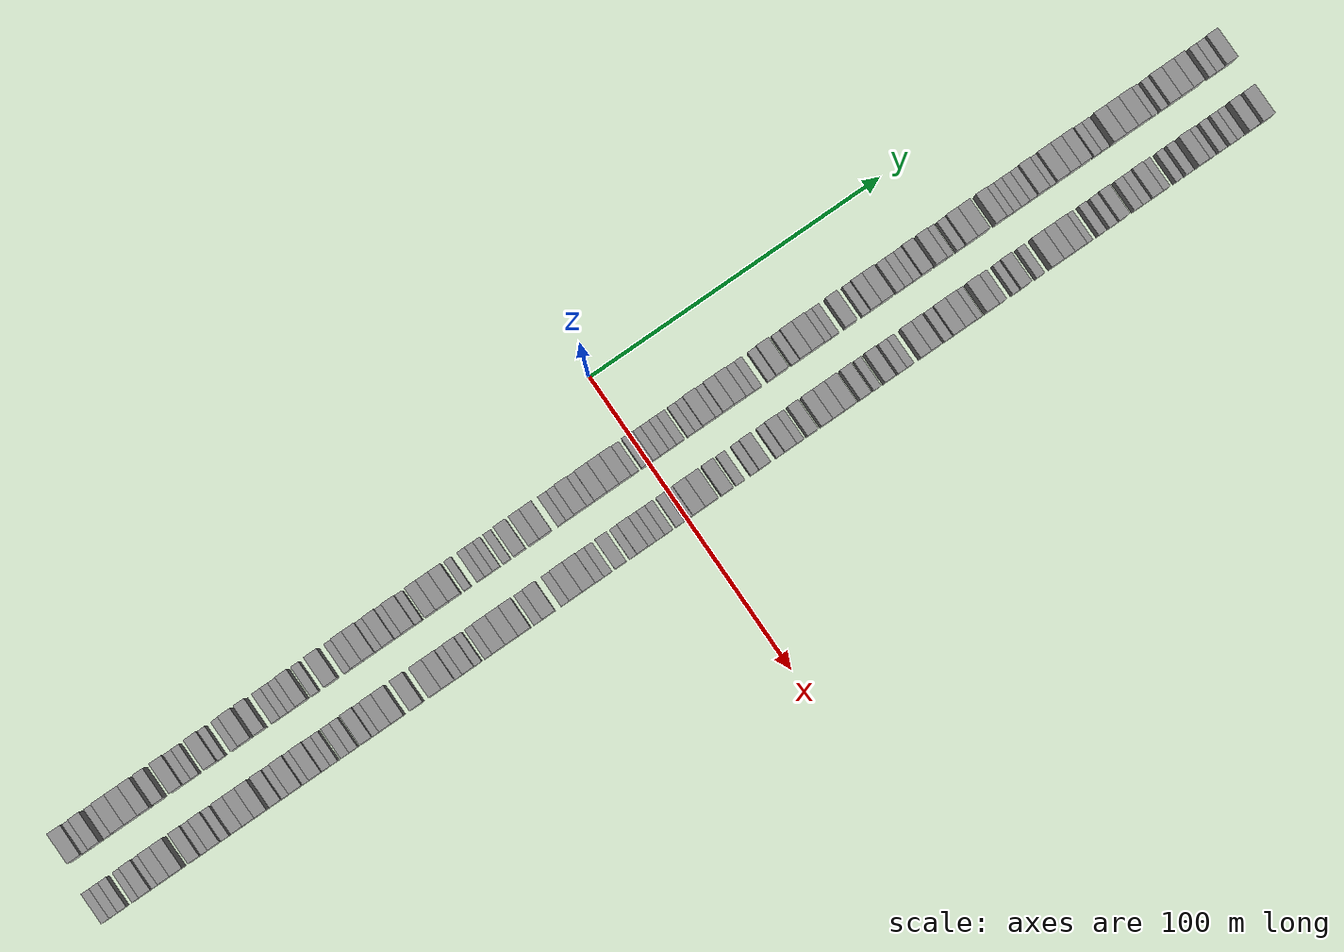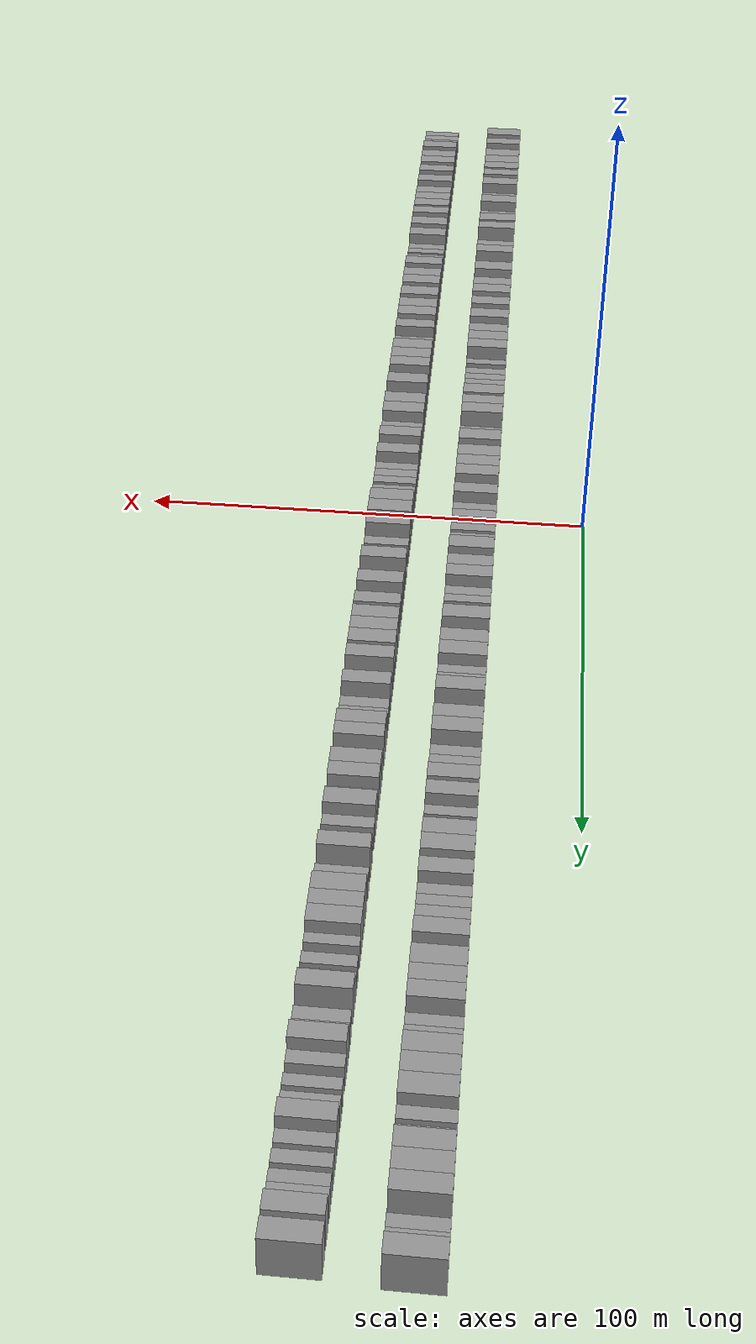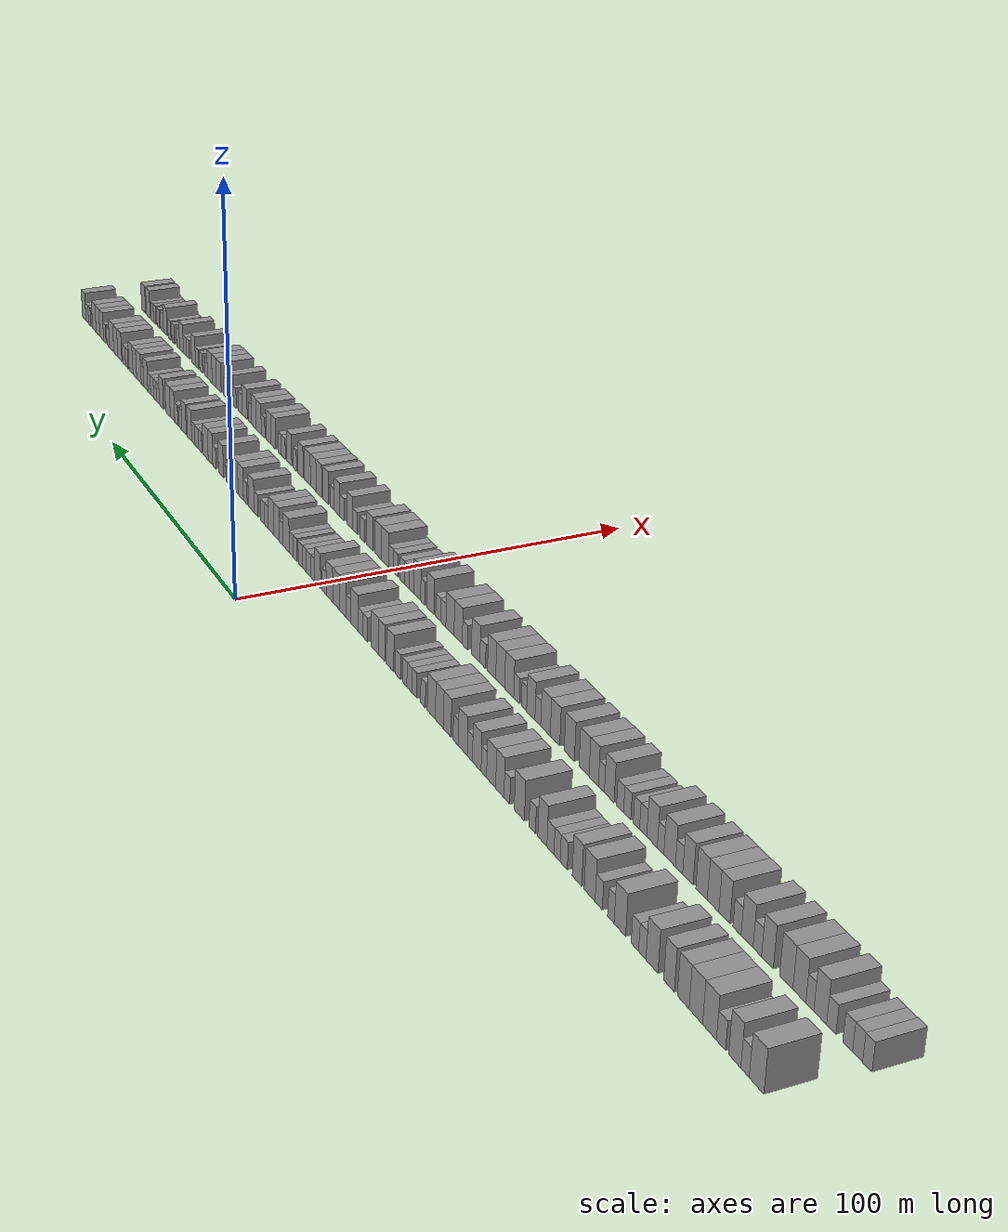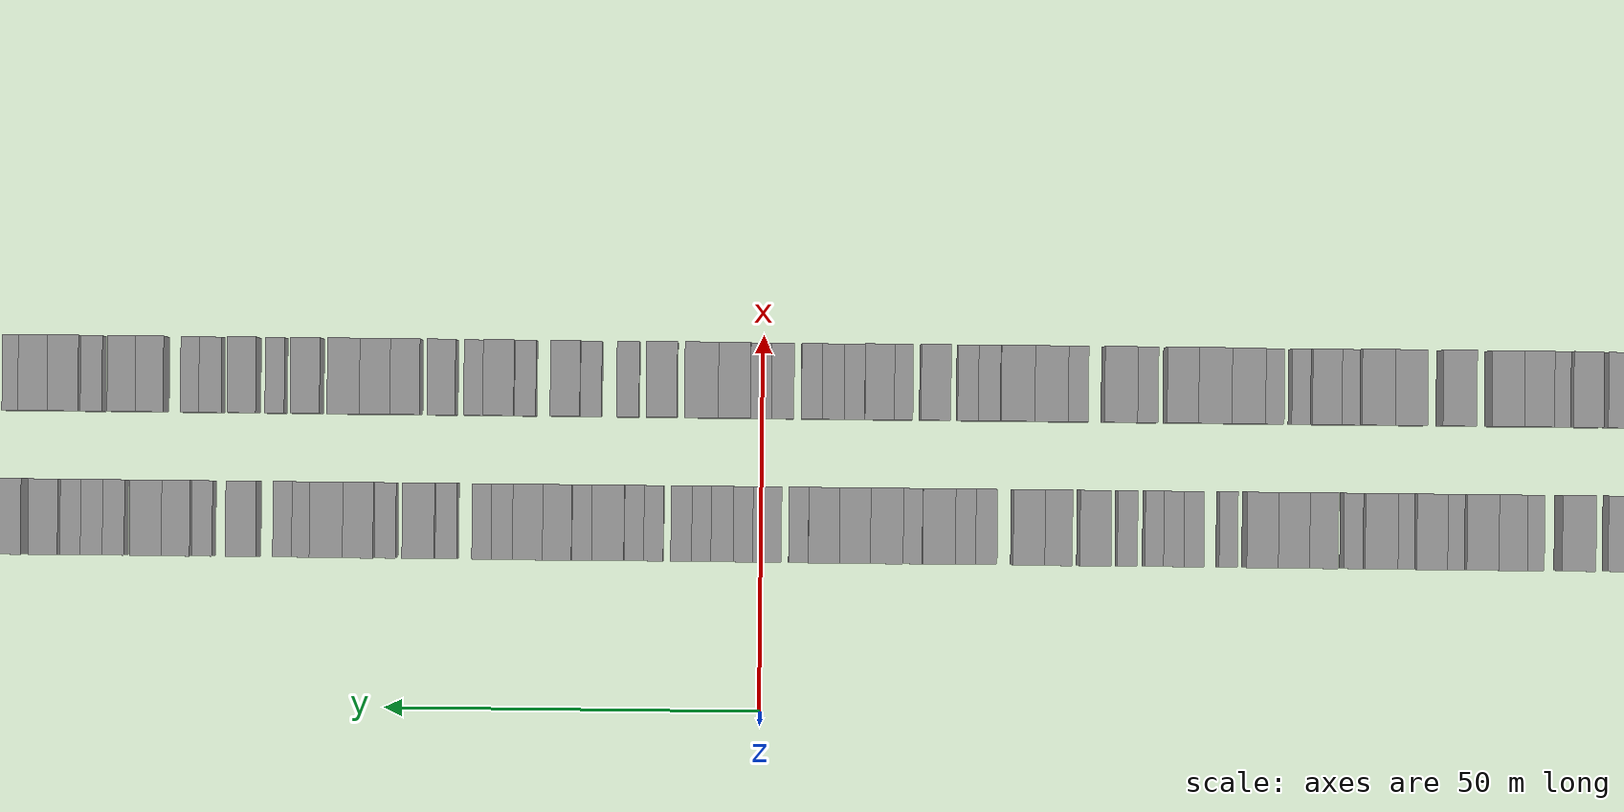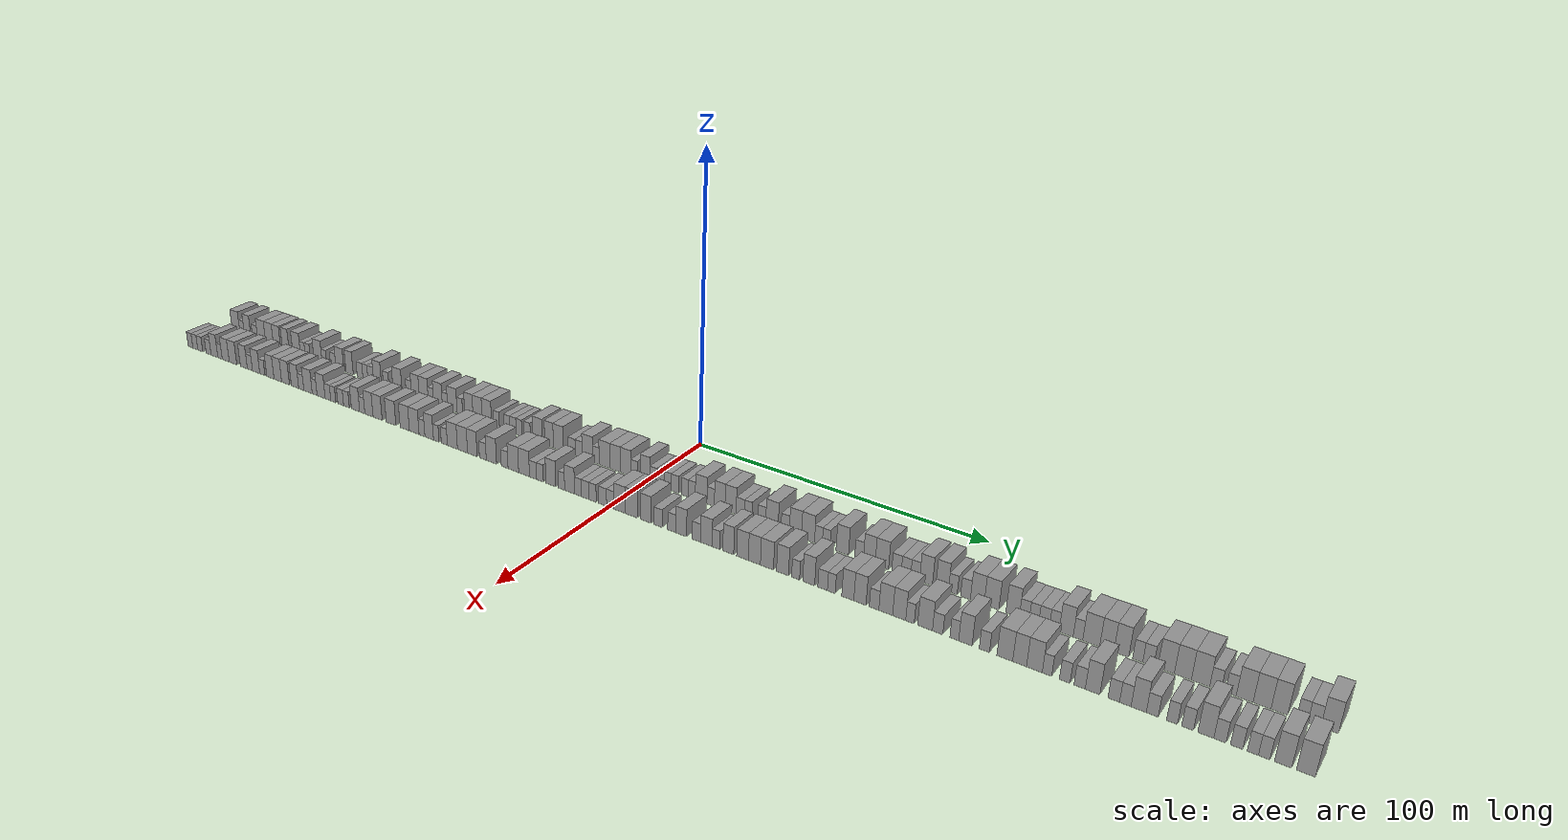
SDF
<sdf version="1.6">
 <world name="default">
  <scene>
   <sky><clouds><speed>12</speed></clouds></sky>
   <ambient>0.4 0.4 0.4 1</ambient>
   <background>0.7 0.7 0.7 1</background>
   <shadows>1</shadows>
  </scene>
  <gravity>0 0 -9.8066</gravity>
  <magnetic_field>6e-06 2.3e-05 -4.2e-05</magnetic_field>
  <physics default="0" name="default_physics" type="ode">
   <ode>
    <solver>
     <type>quick</type>
     <iters>10</iters>
     <sor>1.0</sor>
     <use_dynamic_moi_rescaling>0</use_dynamic_moi_rescaling>
    </solver>
    <constraints>
     <cfm>0</cfm>
     <erp>0.2</erp>
     <contact_max_correcting_vel>100</contact_max_correcting_vel>
     <contact_surface_layer>0.001</contact_surface_layer>
    </constraints>
   </ode>
   <max_step_size>0.004</max_step_size>
   <real_time_factor>1</real_time_factor>
   <real_time_update_rate>250</real_time_update_rate>
  </physics>
  <light name="sun" type="directional">
   <pose>0 0 10 0 0 0</pose>
   <diffuse>0.8 0.8 0.8 1</diffuse>
   <specular>0.2 0.2 0.2 1</specular>
   <attenuation>
    <range>1000</range>
    <constant>0.9</constant>
    <linear>0.01</linear>
    <quadratic>0.001</quadratic>
   </attenuation>
   <direction>-0.5 0.1 -0.9</direction>
  </light>
  <model name="building_1">
   <static>0</static>
   <pose>25.0000 -193.7924 0 0.000000 0.000000 0.000000</pose>
   <link name="link">
    <pose>0 0 4.50 0 0 0</pose>
    <collision name="collision"><geometry><box><size>10.0000 4.4152 9.0000</size></box></geometry></collision>
    <visual name="visual">
     <cast_shadows>0</cast_shadows>
     <geometry><box><size>10.0000 4.4152 9.0000</size></box></geometry>
     <material>
      <script>
       <uri>model://grey_wall/materials/scripts</uri>
       <uri>model://grey_wall/materials/textures</uri>
       <name>vrc/grey_wall</name>
      </script>
     </material>
    </visual>
   </link>
  </model>
  <model name="building_2">
   <static>1</static>
   <pose>25.0000 -190.3012 0 0.000000 0.000000 0.000000</pose>
   <link name="link">
    <pose>0 0 3.00 0 0 0</pose>
    <collision name="collision"><geometry><box><size>10.0000 2.5671 6.0000</size></box></geometry></collision>
    <visual name="visual">
     <cast_shadows>0</cast_shadows>
     <geometry><box><size>10.0000 2.5671 6.0000</size></box></geometry>
     <material>
      <script>
       <uri>model://grey_wall/materials/scripts</uri>
       <uri>model://grey_wall/materials/textures</uri>
       <name>vrc/grey_wall</name>
      </script>
     </material>
    </visual>
   </link>
  </model>
  <model name="building_3">
   <static>1</static>
   <pose>25.0000 -187.1468 0 0.000000 0.000000 0.000000</pose>
   <link name="link">
    <pose>0 0 4.50 0 0 0</pose>
    <collision name="collision"><geometry><box><size>10.0000 3.7419 9.0000</size></box></geometry></collision>
    <visual name="visual">
     <cast_shadows>0</cast_shadows>
     <geometry><box><size>10.0000 3.7419 9.0000</size></box></geometry>
     <material>
      <script>
       <uri>model://grey_wall/materials/scripts</uri>
       <uri>model://grey_wall/materials/textures</uri>
       <name>vrc/grey_wall</name>
      </script>
     </material>
    </visual>
   </link>
  </model>
  <model name="building_4">
   <static>1</static>
   <pose>25.0000 -182.8358 0 0.000000 0.000000 0.000000</pose>
   <link name="link">
    <pose>0 0 3.00 0 0 0</pose>
    <collision name="collision"><geometry><box><size>10.0000 2.8802 6.0000</size></box></geometry></collision>
    <visual name="visual">
     <cast_shadows>0</cast_shadows>
     <geometry><box><size>10.0000 2.8802 6.0000</size></box></geometry>
     <material>
      <script>
       <uri>model://grey_wall/materials/scripts</uri>
       <uri>model://grey_wall/materials/textures</uri>
       <name>vrc/grey_wall</name>
      </script>
     </material>
    </visual>
   </link>
  </model>
  <model name="building_5">
   <static>1</static>
   <pose>25.0000 -179.1639 0 0.000000 0.000000 0.000000</pose>
   <link name="link">
    <pose>0 0 4.50 0 0 0</pose>
    <collision name="collision"><geometry><box><size>10.0000 4.4635 9.0000</size></box></geometry></collision>
    <visual name="visual">
     <cast_shadows>0</cast_shadows>
     <geometry><box><size>10.0000 4.4635 9.0000</size></box></geometry>
     <material>
      <script>
       <uri>model://grey_wall/materials/scripts</uri>
       <uri>model://grey_wall/materials/textures</uri>
       <name>vrc/grey_wall</name>
      </script>
     </material>
    </visual>
   </link>
  </model>
  <model name="building_6">
   <static>1</static>
   <pose>25.0000 -174.7118 0 0.000000 0.000000 0.000000</pose>
   <link name="link">
    <pose>0 0 4.50 0 0 0</pose>
    <collision name="collision"><geometry><box><size>10.0000 4.4406 9.0000</size></box></geometry></collision>
    <visual name="visual">
     <cast_shadows>0</cast_shadows>
     <geometry><box><size>10.0000 4.4406 9.0000</size></box></geometry>
     <material>
      <script>
       <uri>model://grey_wall/materials/scripts</uri>
       <uri>model://grey_wall/materials/textures</uri>
       <name>vrc/grey_wall</name>
      </script>
     </material>
    </visual>
   </link>
  </model>
  <model name="building_7">
   <static>1</static>
   <pose>25.0000 -170.5150 0 0.000000 0.000000 0.000000</pose>
   <link name="link">
    <pose>0 0 4.50 0 0 0</pose>
    <collision name="collision"><geometry><box><size>10.0000 3.9530 9.0000</size></box></geometry></collision>
    <visual name="visual">
     <cast_shadows>0</cast_shadows>
     <geometry><box><size>10.0000 3.9530 9.0000</size></box></geometry>
     <material>
      <script>
       <uri>model://grey_wall/materials/scripts</uri>
       <uri>model://grey_wall/materials/textures</uri>
       <name>vrc/grey_wall</name>
      </script>
     </material>
    </visual>
   </link>
  </model>
  <model name="building_8">
   <static>1</static>
   <pose>25.0000 -165.7242 0 0.000000 0.000000 0.000000</pose>
   <link name="link">
    <pose>0 0 4.50 0 0 0</pose>
    <collision name="collision"><geometry><box><size>10.0000 3.6286 9.0000</size></box></geometry></collision>
    <visual name="visual">
     <cast_shadows>0</cast_shadows>
     <geometry><box><size>10.0000 3.6286 9.0000</size></box></geometry>
     <material>
      <script>
       <uri>model://grey_wall/materials/scripts</uri>
       <uri>model://grey_wall/materials/textures</uri>
       <name>vrc/grey_wall</name>
      </script>
     </material>
    </visual>
   </link>
  </model>
  <model name="building_9">
   <static>1</static>
   <pose>25.0000 -159.7972 0 0.000000 0.000000 0.000000</pose>
   <link name="link">
    <pose>0 0 4.50 0 0 0</pose>
    <collision name="collision"><geometry><box><size>10.0000 4.2253 9.0000</size></box></geometry></collision>
    <visual name="visual">
     <cast_shadows>0</cast_shadows>
     <geometry><box><size>10.0000 4.2253 9.0000</size></box></geometry>
     <material>
      <script>
       <uri>model://grey_wall/materials/scripts</uri>
       <uri>model://grey_wall/materials/textures</uri>
       <name>vrc/grey_wall</name>
      </script>
     </material>
    </visual>
   </link>
  </model>
  <model name="building_10">
   <static>1</static>
   <pose>25.0000 -156.3701 0 0.000000 0.000000 0.000000</pose>
   <link name="link">
    <pose>0 0 3.00 0 0 0</pose>
    <collision name="collision"><geometry><box><size>10.0000 2.6289 6.0000</size></box></geometry></collision>
    <visual name="visual">
     <cast_shadows>0</cast_shadows>
     <geometry><box><size>10.0000 2.6289 6.0000</size></box></geometry>
     <material>
      <script>
       <uri>model://grey_wall/materials/scripts</uri>
       <uri>model://grey_wall/materials/textures</uri>
       <name>vrc/grey_wall</name>
      </script>
     </material>
    </visual>
   </link>
  </model>
  <model name="building_11">
   <static>1</static>
   <pose>25.0000 -153.7087 0 0.000000 0.000000 0.000000</pose>
   <link name="link">
    <pose>0 0 3.00 0 0 0</pose>
    <collision name="collision"><geometry><box><size>10.0000 2.6939 6.0000</size></box></geometry></collision>
    <visual name="visual">
     <cast_shadows>0</cast_shadows>
     <geometry><box><size>10.0000 2.6939 6.0000</size></box></geometry>
     <material>
      <script>
       <uri>model://grey_wall/materials/scripts</uri>
       <uri>model://grey_wall/materials/textures</uri>
       <name>vrc/grey_wall</name>
      </script>
     </material>
    </visual>
   </link>
  </model>
  <model name="building_12">
   <static>1</static>
   <pose>25.0000 -148.2221 0 0.000000 0.000000 0.000000</pose>
   <link name="link">
    <pose>0 0 4.50 0 0 0</pose>
    <collision name="collision"><geometry><box><size>10.0000 4.2792 9.0000</size></box></geometry></collision>
    <visual name="visual">
     <cast_shadows>0</cast_shadows>
     <geometry><box><size>10.0000 4.2792 9.0000</size></box></geometry>
     <material>
      <script>
       <uri>model://grey_wall/materials/scripts</uri>
       <uri>model://grey_wall/materials/textures</uri>
       <name>vrc/grey_wall</name>
      </script>
     </material>
    </visual>
   </link>
  </model>
  <model name="building_13">
   <static>1</static>
   <pose>25.0000 -144.8468 0 0.000000 0.000000 0.000000</pose>
   <link name="link">
    <pose>0 0 3.00 0 0 0</pose>
    <collision name="collision"><geometry><box><size>10.0000 2.4714 6.0000</size></box></geometry></collision>
    <visual name="visual">
     <cast_shadows>0</cast_shadows>
     <geometry><box><size>10.0000 2.4714 6.0000</size></box></geometry>
     <material>
      <script>
       <uri>model://grey_wall/materials/scripts</uri>
       <uri>model://grey_wall/materials/textures</uri>
       <name>vrc/grey_wall</name>
      </script>
     </material>
    </visual>
   </link>
  </model>
  <model name="building_14">
   <static>1</static>
   <pose>25.0000 -140.2355 0 0.000000 0.000000 0.000000</pose>
   <link name="link">
    <pose>0 0 3.00 0 0 0</pose>
    <collision name="collision"><geometry><box><size>10.0000 2.7512 6.0000</size></box></geometry></collision>
    <visual name="visual">
     <cast_shadows>0</cast_shadows>
     <geometry><box><size>10.0000 2.7512 6.0000</size></box></geometry>
     <material>
      <script>
       <uri>model://grey_wall/materials/scripts</uri>
       <uri>model://grey_wall/materials/textures</uri>
       <name>vrc/grey_wall</name>
      </script>
     </material>
    </visual>
   </link>
  </model>
  <model name="building_15">
   <static>1</static>
   <pose>25.0000 -136.7454 0 0.000000 0.000000 0.000000</pose>
   <link name="link">
    <pose>0 0 4.50 0 0 0</pose>
    <collision name="collision"><geometry><box><size>10.0000 4.2292 9.0000</size></box></geometry></collision>
    <visual name="visual">
     <cast_shadows>0</cast_shadows>
     <geometry><box><size>10.0000 4.2292 9.0000</size></box></geometry>
     <material>
      <script>
       <uri>model://grey_wall/materials/scripts</uri>
       <uri>model://grey_wall/materials/textures</uri>
       <name>vrc/grey_wall</name>
      </script>
     </material>
    </visual>
   </link>
  </model>
  <model name="building_16">
   <static>1</static>
   <pose>25.0000 -131.7684 0 0.000000 0.000000 0.000000</pose>
   <link name="link">
    <pose>0 0 4.50 0 0 0</pose>
    <collision name="collision"><geometry><box><size>10.0000 3.7248 9.0000</size></box></geometry></collision>
    <visual name="visual">
     <cast_shadows>0</cast_shadows>
     <geometry><box><size>10.0000 3.7248 9.0000</size></box></geometry>
     <material>
      <script>
       <uri>model://grey_wall/materials/scripts</uri>
       <uri>model://grey_wall/materials/textures</uri>
       <name>vrc/grey_wall</name>
      </script>
     </material>
    </visual>
   </link>
  </model>
  <model name="building_17">
   <static>1</static>
   <pose>25.0000 -126.4617 0 0.000000 0.000000 0.000000</pose>
   <link name="link">
    <pose>0 0 3.00 0 0 0</pose>
    <collision name="collision"><geometry><box><size>10.0000 2.8886 6.0000</size></box></geometry></collision>
    <visual name="visual">
     <cast_shadows>0</cast_shadows>
     <geometry><box><size>10.0000 2.8886 6.0000</size></box></geometry>
     <material>
      <script>
       <uri>model://grey_wall/materials/scripts</uri>
       <uri>model://grey_wall/materials/textures</uri>
       <name>vrc/grey_wall</name>
      </script>
     </material>
    </visual>
   </link>
  </model>
  <model name="building_18">
   <static>1</static>
   <pose>25.0000 -123.7421 0 0.000000 0.000000 0.000000</pose>
   <link name="link">
    <pose>0 0 3.00 0 0 0</pose>
    <collision name="collision"><geometry><box><size>10.0000 2.5507 6.0000</size></box></geometry></collision>
    <visual name="visual">
     <cast_shadows>0</cast_shadows>
     <geometry><box><size>10.0000 2.5507 6.0000</size></box></geometry>
     <material>
      <script>
       <uri>model://grey_wall/materials/scripts</uri>
       <uri>model://grey_wall/materials/textures</uri>
       <name>vrc/grey_wall</name>
      </script>
     </material>
    </visual>
   </link>
  </model>
  <model name="building_19">
   <static>1</static>
   <pose>25.0000 -121.0176 0 0.000000 0.000000 0.000000</pose>
   <link name="link">
    <pose>0 0 3.00 0 0 0</pose>
    <collision name="collision"><geometry><box><size>10.0000 2.8985 6.0000</size></box></geometry></collision>
    <visual name="visual">
     <cast_shadows>0</cast_shadows>
     <geometry><box><size>10.0000 2.8985 6.0000</size></box></geometry>
     <material>
      <script>
       <uri>model://grey_wall/materials/scripts</uri>
       <uri>model://grey_wall/materials/textures</uri>
       <name>vrc/grey_wall</name>
      </script>
     </material>
    </visual>
   </link>
  </model>
  <model name="building_20">
   <static>1</static>
   <pose>25.0000 -117.6397 0 0.000000 0.000000 0.000000</pose>
   <link name="link">
    <pose>0 0 4.50 0 0 0</pose>
    <collision name="collision"><geometry><box><size>10.0000 3.8573 9.0000</size></box></geometry></collision>
    <visual name="visual">
     <cast_shadows>0</cast_shadows>
     <geometry><box><size>10.0000 3.8573 9.0000</size></box></geometry>
     <material>
      <script>
       <uri>model://grey_wall/materials/scripts</uri>
       <uri>model://grey_wall/materials/textures</uri>
       <name>vrc/grey_wall</name>
      </script>
     </material>
    </visual>
   </link>
  </model>
  <model name="building_21">
   <static>1</static>
   <pose>25.0000 -113.3407 0 0.000000 0.000000 0.000000</pose>
   <link name="link">
    <pose>0 0 3.00 0 0 0</pose>
    <collision name="collision"><geometry><box><size>10.0000 2.7407 6.0000</size></box></geometry></collision>
    <visual name="visual">
     <cast_shadows>0</cast_shadows>
     <geometry><box><size>10.0000 2.7407 6.0000</size></box></geometry>
     <material>
      <script>
       <uri>model://grey_wall/materials/scripts</uri>
       <uri>model://grey_wall/materials/textures</uri>
       <name>vrc/grey_wall</name>
      </script>
     </material>
    </visual>
   </link>
  </model>
  <model name="building_22">
   <static>1</static>
   <pose>25.0000 -107.7501 0 0.000000 0.000000 0.000000</pose>
   <link name="link">
    <pose>0 0 4.50 0 0 0</pose>
    <collision name="collision"><geometry><box><size>10.0000 4.4406 9.0000</size></box></geometry></collision>
    <visual name="visual">
     <cast_shadows>0</cast_shadows>
     <geometry><box><size>10.0000 4.4406 9.0000</size></box></geometry>
     <material>
      <script>
       <uri>model://grey_wall/materials/scripts</uri>
       <uri>model://grey_wall/materials/textures</uri>
       <name>vrc/grey_wall</name>
      </script>
     </material>
    </visual>
   </link>
  </model>
  <model name="building_23">
   <static>1</static>
   <pose>25.0000 -102.2286 0 0.000000 0.000000 0.000000</pose>
   <link name="link">
    <pose>0 0 3.00 0 0 0</pose>
    <collision name="collision"><geometry><box><size>10.0000 2.6023 6.0000</size></box></geometry></collision>
    <visual name="visual">
     <cast_shadows>0</cast_shadows>
     <geometry><box><size>10.0000 2.6023 6.0000</size></box></geometry>
     <material>
      <script>
       <uri>model://grey_wall/materials/scripts</uri>
       <uri>model://grey_wall/materials/textures</uri>
       <name>vrc/grey_wall</name>
      </script>
     </material>
    </visual>
   </link>
  </model>
  <model name="building_24">
   <static>1</static>
   <pose>25.0000 -99.0529 0 0.000000 0.000000 0.000000</pose>
   <link name="link">
    <pose>0 0 4.50 0 0 0</pose>
    <collision name="collision"><geometry><box><size>10.0000 3.7491 9.0000</size></box></geometry></collision>
    <visual name="visual">
     <cast_shadows>0</cast_shadows>
     <geometry><box><size>10.0000 3.7491 9.0000</size></box></geometry>
     <material>
      <script>
       <uri>model://grey_wall/materials/scripts</uri>
       <uri>model://grey_wall/materials/textures</uri>
       <name>vrc/grey_wall</name>
      </script>
     </material>
    </visual>
   </link>
  </model>
  <model name="building_25">
   <static>1</static>
   <pose>25.0000 -95.0682 0 0.000000 0.000000 0.000000</pose>
   <link name="link">
    <pose>0 0 4.50 0 0 0</pose>
    <collision name="collision"><geometry><box><size>10.0000 4.2203 9.0000</size></box></geometry></collision>
    <visual name="visual">
     <cast_shadows>0</cast_shadows>
     <geometry><box><size>10.0000 4.2203 9.0000</size></box></geometry>
     <material>
      <script>
       <uri>model://grey_wall/materials/scripts</uri>
       <uri>model://grey_wall/materials/textures</uri>
       <name>vrc/grey_wall</name>
      </script>
     </material>
    </visual>
   </link>
  </model>
  <model name="building_26">
   <static>1</static>
   <pose>25.0000 -91.6894 0 0.000000 0.000000 0.000000</pose>
   <link name="link">
    <pose>0 0 3.00 0 0 0</pose>
    <collision name="collision"><geometry><box><size>10.0000 2.5374 6.0000</size></box></geometry></collision>
    <visual name="visual">
     <cast_shadows>0</cast_shadows>
     <geometry><box><size>10.0000 2.5374 6.0000</size></box></geometry>
     <material>
      <script>
       <uri>model://grey_wall/materials/scripts</uri>
       <uri>model://grey_wall/materials/textures</uri>
       <name>vrc/grey_wall</name>
      </script>
     </material>
    </visual>
   </link>
  </model>
  <model name="building_27">
   <static>1</static>
   <pose>25.0000 -88.3785 0 0.000000 0.000000 0.000000</pose>
   <link name="link">
    <pose>0 0 4.50 0 0 0</pose>
    <collision name="collision"><geometry><box><size>10.0000 4.0845 9.0000</size></box></geometry></collision>
    <visual name="visual">
     <cast_shadows>0</cast_shadows>
     <geometry><box><size>10.0000 4.0845 9.0000</size></box></geometry>
     <material>
      <script>
       <uri>model://grey_wall/materials/scripts</uri>
       <uri>model://grey_wall/materials/textures</uri>
       <name>vrc/grey_wall</name>
      </script>
     </material>
    </visual>
   </link>
  </model>
  <model name="building_28">
   <static>1</static>
   <pose>25.0000 -85.1042 0 0.000000 0.000000 0.000000</pose>
   <link name="link">
    <pose>0 0 3.00 0 0 0</pose>
    <collision name="collision"><geometry><box><size>10.0000 2.4640 6.0000</size></box></geometry></collision>
    <visual name="visual">
     <cast_shadows>0</cast_shadows>
     <geometry><box><size>10.0000 2.4640 6.0000</size></box></geometry>
     <material>
      <script>
       <uri>model://grey_wall/materials/scripts</uri>
       <uri>model://grey_wall/materials/textures</uri>
       <name>vrc/grey_wall</name>
      </script>
     </material>
    </visual>
   </link>
  </model>
  <model name="building_29">
   <static>1</static>
   <pose>25.0000 -81.7044 0 0.000000 0.000000 0.000000</pose>
   <link name="link">
    <pose>0 0 4.50 0 0 0</pose>
    <collision name="collision"><geometry><box><size>10.0000 4.3356 9.0000</size></box></geometry></collision>
    <visual name="visual">
     <cast_shadows>0</cast_shadows>
     <geometry><box><size>10.0000 4.3356 9.0000</size></box></geometry>
     <material>
      <script>
       <uri>model://grey_wall/materials/scripts</uri>
       <uri>model://grey_wall/materials/textures</uri>
       <name>vrc/grey_wall</name>
      </script>
     </material>
    </visual>
   </link>
  </model>
  <model name="building_30">
   <static>1</static>
   <pose>25.0000 -78.2587 0 0.000000 0.000000 0.000000</pose>
   <link name="link">
    <pose>0 0 3.00 0 0 0</pose>
    <collision name="collision"><geometry><box><size>10.0000 2.5559 6.0000</size></box></geometry></collision>
    <visual name="visual">
     <cast_shadows>0</cast_shadows>
     <geometry><box><size>10.0000 2.5559 6.0000</size></box></geometry>
     <material>
      <script>
       <uri>model://grey_wall/materials/scripts</uri>
       <uri>model://grey_wall/materials/textures</uri>
       <name>vrc/grey_wall</name>
      </script>
     </material>
    </visual>
   </link>
  </model>
  <model name="building_31">
   <static>1</static>
   <pose>25.0000 -74.0989 0 0.000000 0.000000 0.000000</pose>
   <link name="link">
    <pose>0 0 4.50 0 0 0</pose>
    <collision name="collision"><geometry><box><size>10.0000 3.7637 9.0000</size></box></geometry></collision>
    <visual name="visual">
     <cast_shadows>0</cast_shadows>
     <geometry><box><size>10.0000 3.7637 9.0000</size></box></geometry>
     <material>
      <script>
       <uri>model://grey_wall/materials/scripts</uri>
       <uri>model://grey_wall/materials/textures</uri>
       <name>vrc/grey_wall</name>
      </script>
     </material>
    </visual>
   </link>
  </model>
  <model name="building_32">
   <static>1</static>
   <pose>25.0000 -70.1562 0 0.000000 0.000000 0.000000</pose>
   <link name="link">
    <pose>0 0 4.50 0 0 0</pose>
    <collision name="collision"><geometry><box><size>10.0000 4.1217 9.0000</size></box></geometry></collision>
    <visual name="visual">
     <cast_shadows>0</cast_shadows>
     <geometry><box><size>10.0000 4.1217 9.0000</size></box></geometry>
     <material>
      <script>
       <uri>model://grey_wall/materials/scripts</uri>
       <uri>model://grey_wall/materials/textures</uri>
       <name>vrc/grey_wall</name>
      </script>
     </material>
    </visual>
   </link>
  </model>
  <model name="building_33">
   <static>1</static>
   <pose>25.0000 -66.0154 0 0.000000 0.000000 0.000000</pose>
   <link name="link">
    <pose>0 0 4.50 0 0 0</pose>
    <collision name="collision"><geometry><box><size>10.0000 4.1598 9.0000</size></box></geometry></collision>
    <visual name="visual">
     <cast_shadows>0</cast_shadows>
     <geometry><box><size>10.0000 4.1598 9.0000</size></box></geometry>
     <material>
      <script>
       <uri>model://grey_wall/materials/scripts</uri>
       <uri>model://grey_wall/materials/textures</uri>
       <name>vrc/grey_wall</name>
      </script>
     </material>
    </visual>
   </link>
  </model>
  <model name="building_34">
   <static>1</static>
   <pose>25.0000 -61.7127 0 0.000000 0.000000 0.000000</pose>
   <link name="link">
    <pose>0 0 3.00 0 0 0</pose>
    <collision name="collision"><geometry><box><size>10.0000 2.4456 6.0000</size></box></geometry></collision>
    <visual name="visual">
     <cast_shadows>0</cast_shadows>
     <geometry><box><size>10.0000 2.4456 6.0000</size></box></geometry>
     <material>
      <script>
       <uri>model://grey_wall/materials/scripts</uri>
       <uri>model://grey_wall/materials/textures</uri>
       <name>vrc/grey_wall</name>
      </script>
     </material>
    </visual>
   </link>
  </model>
  <model name="building_35">
   <static>1</static>
   <pose>25.0000 -57.1647 0 0.000000 0.000000 0.000000</pose>
   <link name="link">
    <pose>0 0 3.00 0 0 0</pose>
    <collision name="collision"><geometry><box><size>10.0000 2.6504 6.0000</size></box></geometry></collision>
    <visual name="visual">
     <cast_shadows>0</cast_shadows>
     <geometry><box><size>10.0000 2.6504 6.0000</size></box></geometry>
     <material>
      <script>
       <uri>model://grey_wall/materials/scripts</uri>
       <uri>model://grey_wall/materials/textures</uri>
       <name>vrc/grey_wall</name>
      </script>
     </material>
    </visual>
   </link>
  </model>
  <model name="building_36">
   <static>1</static>
   <pose>25.0000 -54.4928 0 0.000000 0.000000 0.000000</pose>
   <link name="link">
    <pose>0 0 3.00 0 0 0</pose>
    <collision name="collision"><geometry><box><size>10.0000 2.6936 6.0000</size></box></geometry></collision>
    <visual name="visual">
     <cast_shadows>0</cast_shadows>
     <geometry><box><size>10.0000 2.6936 6.0000</size></box></geometry>
     <material>
      <script>
       <uri>model://grey_wall/materials/scripts</uri>
       <uri>model://grey_wall/materials/textures</uri>
       <name>vrc/grey_wall</name>
      </script>
     </material>
    </visual>
   </link>
  </model>
  <model name="building_37">
   <static>1</static>
   <pose>25.0000 -51.9126 0 0.000000 0.000000 0.000000</pose>
   <link name="link">
    <pose>0 0 3.00 0 0 0</pose>
    <collision name="collision"><geometry><box><size>10.0000 2.4667 6.0000</size></box></geometry></collision>
    <visual name="visual">
     <cast_shadows>0</cast_shadows>
     <geometry><box><size>10.0000 2.4667 6.0000</size></box></geometry>
     <material>
      <script>
       <uri>model://grey_wall/materials/scripts</uri>
       <uri>model://grey_wall/materials/textures</uri>
       <name>vrc/grey_wall</name>
      </script>
     </material>
    </visual>
   </link>
  </model>
  <model name="building_38">
   <static>1</static>
   <pose>25.0000 -48.3581 0 0.000000 0.000000 0.000000</pose>
   <link name="link">
    <pose>0 0 3.00 0 0 0</pose>
    <collision name="collision"><geometry><box><size>10.0000 2.6423 6.0000</size></box></geometry></collision>
    <visual name="visual">
     <cast_shadows>0</cast_shadows>
     <geometry><box><size>10.0000 2.6423 6.0000</size></box></geometry>
     <material>
      <script>
       <uri>model://grey_wall/materials/scripts</uri>
       <uri>model://grey_wall/materials/textures</uri>
       <name>vrc/grey_wall</name>
      </script>
     </material>
    </visual>
   </link>
  </model>
  <model name="building_39">
   <static>1</static>
   <pose>25.0000 -43.9781 0 0.000000 0.000000 0.000000</pose>
   <link name="link">
    <pose>0 0 4.50 0 0 0</pose>
    <collision name="collision"><geometry><box><size>10.0000 4.1177 9.0000</size></box></geometry></collision>
    <visual name="visual">
     <cast_shadows>0</cast_shadows>
     <geometry><box><size>10.0000 4.1177 9.0000</size></box></geometry>
     <material>
      <script>
       <uri>model://grey_wall/materials/scripts</uri>
       <uri>model://grey_wall/materials/textures</uri>
       <name>vrc/grey_wall</name>
      </script>
     </material>
    </visual>
   </link>
  </model>
  <model name="building_40">
   <static>1</static>
   <pose>25.0000 -39.1123 0 0.000000 0.000000 0.000000</pose>
   <link name="link">
    <pose>0 0 4.50 0 0 0</pose>
    <collision name="collision"><geometry><box><size>10.0000 3.6139 9.0000</size></box></geometry></collision>
    <visual name="visual">
     <cast_shadows>0</cast_shadows>
     <geometry><box><size>10.0000 3.6139 9.0000</size></box></geometry>
     <material>
      <script>
       <uri>model://grey_wall/materials/scripts</uri>
       <uri>model://grey_wall/materials/textures</uri>
       <name>vrc/grey_wall</name>
      </script>
     </material>
    </visual>
   </link>
  </model>
  <model name="building_41">
   <static>1</static>
   <pose>25.0000 -35.2139 0 0.000000 0.000000 0.000000</pose>
   <link name="link">
    <pose>0 0 4.50 0 0 0</pose>
    <collision name="collision"><geometry><box><size>10.0000 4.1830 9.0000</size></box></geometry></collision>
    <visual name="visual">
     <cast_shadows>0</cast_shadows>
     <geometry><box><size>10.0000 4.1830 9.0000</size></box></geometry>
     <material>
      <script>
       <uri>model://grey_wall/materials/scripts</uri>
       <uri>model://grey_wall/materials/textures</uri>
       <name>vrc/grey_wall</name>
      </script>
     </material>
    </visual>
   </link>
  </model>
  <model name="building_42">
   <static>1</static>
   <pose>25.0000 -29.6990 0 0.000000 0.000000 0.000000</pose>
   <link name="link">
    <pose>0 0 3.00 0 0 0</pose>
    <collision name="collision"><geometry><box><size>10.0000 2.8468 6.0000</size></box></geometry></collision>
    <visual name="visual">
     <cast_shadows>0</cast_shadows>
     <geometry><box><size>10.0000 2.8468 6.0000</size></box></geometry>
     <material>
      <script>
       <uri>model://grey_wall/materials/scripts</uri>
       <uri>model://grey_wall/materials/textures</uri>
       <name>vrc/grey_wall</name>
      </script>
     </material>
    </visual>
   </link>
  </model>
  <model name="building_43">
   <static>1</static>
   <pose>25.0000 -26.8879 0 0.000000 0.000000 0.000000</pose>
   <link name="link">
    <pose>0 0 3.00 0 0 0</pose>
    <collision name="collision"><geometry><box><size>10.0000 2.7754 6.0000</size></box></geometry></collision>
    <visual name="visual">
     <cast_shadows>0</cast_shadows>
     <geometry><box><size>10.0000 2.7754 6.0000</size></box></geometry>
     <material>
      <script>
       <uri>model://grey_wall/materials/scripts</uri>
       <uri>model://grey_wall/materials/textures</uri>
       <name>vrc/grey_wall</name>
      </script>
     </material>
    </visual>
   </link>
  </model>
  <model name="building_44">
   <static>1</static>
   <pose>25.0000 -23.3511 0 0.000000 0.000000 0.000000</pose>
   <link name="link">
    <pose>0 0 4.50 0 0 0</pose>
    <collision name="collision"><geometry><box><size>10.0000 4.2981 9.0000</size></box></geometry></collision>
    <visual name="visual">
     <cast_shadows>0</cast_shadows>
     <geometry><box><size>10.0000 4.2981 9.0000</size></box></geometry>
     <material>
      <script>
       <uri>model://grey_wall/materials/scripts</uri>
       <uri>model://grey_wall/materials/textures</uri>
       <name>vrc/grey_wall</name>
      </script>
     </material>
    </visual>
   </link>
  </model>
  <model name="building_45">
   <static>1</static>
   <pose>25.0000 -19.9102 0 0.000000 0.000000 0.000000</pose>
   <link name="link">
    <pose>0 0 3.00 0 0 0</pose>
    <collision name="collision"><geometry><box><size>10.0000 2.5838 6.0000</size></box></geometry></collision>
    <visual name="visual">
     <cast_shadows>0</cast_shadows>
     <geometry><box><size>10.0000 2.5838 6.0000</size></box></geometry>
     <material>
      <script>
       <uri>model://grey_wall/materials/scripts</uri>
       <uri>model://grey_wall/materials/textures</uri>
       <name>vrc/grey_wall</name>
      </script>
     </material>
    </visual>
   </link>
  </model>
  <model name="building_46">
   <static>1</static>
   <pose>25.0000 -16.4606 0 0.000000 0.000000 0.000000</pose>
   <link name="link">
    <pose>0 0 4.50 0 0 0</pose>
    <collision name="collision"><geometry><box><size>10.0000 4.3153 9.0000</size></box></geometry></collision>
    <visual name="visual">
     <cast_shadows>0</cast_shadows>
     <geometry><box><size>10.0000 4.3153 9.0000</size></box></geometry>
     <material>
      <script>
       <uri>model://grey_wall/materials/scripts</uri>
       <uri>model://grey_wall/materials/textures</uri>
       <name>vrc/grey_wall</name>
      </script>
     </material>
    </visual>
   </link>
  </model>
  <model name="building_47">
   <static>1</static>
   <pose>25.0000 -12.2631 0 0.000000 0.000000 0.000000</pose>
   <link name="link">
    <pose>0 0 4.50 0 0 0</pose>
    <collision name="collision"><geometry><box><size>10.0000 4.0795 9.0000</size></box></geometry></collision>
    <visual name="visual">
     <cast_shadows>0</cast_shadows>
     <geometry><box><size>10.0000 4.0795 9.0000</size></box></geometry>
     <material>
      <script>
       <uri>model://grey_wall/materials/scripts</uri>
       <uri>model://grey_wall/materials/textures</uri>
       <name>vrc/grey_wall</name>
      </script>
     </material>
    </visual>
   </link>
  </model>
  <model name="building_48">
   <static>1</static>
   <pose>25.0000 -8.1758 0 0.000000 0.000000 0.000000</pose>
   <link name="link">
    <pose>0 0 4.50 0 0 0</pose>
    <collision name="collision"><geometry><box><size>10.0000 4.0951 9.0000</size></box></geometry></collision>
    <visual name="visual">
     <cast_shadows>0</cast_shadows>
     <geometry><box><size>10.0000 4.0951 9.0000</size></box></geometry>
     <material>
      <script>
       <uri>model://grey_wall/materials/scripts</uri>
       <uri>model://grey_wall/materials/textures</uri>
       <name>vrc/grey_wall</name>
      </script>
     </material>
    </visual>
   </link>
  </model>
  <model name="building_49">
   <static>1</static>
   <pose>25.0000 -4.8378 0 0.000000 0.000000 0.000000</pose>
   <link name="link">
    <pose>0 0 3.00 0 0 0</pose>
    <collision name="collision"><geometry><box><size>10.0000 2.5807 6.0000</size></box></geometry></collision>
    <visual name="visual">
     <cast_shadows>0</cast_shadows>
     <geometry><box><size>10.0000 2.5807 6.0000</size></box></geometry>
     <material>
      <script>
       <uri>model://grey_wall/materials/scripts</uri>
       <uri>model://grey_wall/materials/textures</uri>
       <name>vrc/grey_wall</name>
      </script>
     </material>
    </visual>
   </link>
  </model>
  <model name="building_50">
   <static>1</static>
   <pose>25.0000 -0.6598 0 0.000000 0.000000 0.000000</pose>
   <link name="link">
    <pose>0 0 4.50 0 0 0</pose>
    <collision name="collision"><geometry><box><size>10.0000 3.7753 9.0000</size></box></geometry></collision>
    <visual name="visual">
     <cast_shadows>0</cast_shadows>
     <geometry><box><size>10.0000 3.7753 9.0000</size></box></geometry>
     <material>
      <script>
       <uri>model://grey_wall/materials/scripts</uri>
       <uri>model://grey_wall/materials/textures</uri>
       <name>vrc/grey_wall</name>
      </script>
     </material>
    </visual>
   </link>
  </model>
  <model name="building_51">
   <static>1</static>
   <pose>25.0000 2.5211 0 0.000000 0.000000 0.000000</pose>
   <link name="link">
    <pose>0 0 3.00 0 0 0</pose>
    <collision name="collision"><geometry><box><size>10.0000 2.5867 6.0000</size></box></geometry></collision>
    <visual name="visual">
     <cast_shadows>0</cast_shadows>
     <geometry><box><size>10.0000 2.5867 6.0000</size></box></geometry>
     <material>
      <script>
       <uri>model://grey_wall/materials/scripts</uri>
       <uri>model://grey_wall/materials/textures</uri>
       <name>vrc/grey_wall</name>
      </script>
     </material>
    </visual>
   </link>
  </model>
  <model name="building_52">
   <static>1</static>
   <pose>25.0000 5.2859 0 0.000000 0.000000 0.000000</pose>
   <link name="link">
    <pose>0 0 3.00 0 0 0</pose>
    <collision name="collision"><geometry><box><size>10.0000 2.9429 6.0000</size></box></geometry></collision>
    <visual name="visual">
     <cast_shadows>0</cast_shadows>
     <geometry><box><size>10.0000 2.9429 6.0000</size></box></geometry>
     <material>
      <script>
       <uri>model://grey_wall/materials/scripts</uri>
       <uri>model://grey_wall/materials/textures</uri>
       <name>vrc/grey_wall</name>
      </script>
     </material>
    </visual>
   </link>
  </model>
  <model name="building_53">
   <static>1</static>
   <pose>25.0000 8.0348 0 0.000000 0.000000 0.000000</pose>
   <link name="link">
    <pose>0 0 3.00 0 0 0</pose>
    <collision name="collision"><geometry><box><size>10.0000 2.5548 6.0000</size></box></geometry></collision>
    <visual name="visual">
     <cast_shadows>0</cast_shadows>
     <geometry><box><size>10.0000 2.5548 6.0000</size></box></geometry>
     <material>
      <script>
       <uri>model://grey_wall/materials/scripts</uri>
       <uri>model://grey_wall/materials/textures</uri>
       <name>vrc/grey_wall</name>
      </script>
     </material>
    </visual>
   </link>
  </model>
  <model name="building_54">
   <static>1</static>
   <pose>25.0000 10.6931 0 0.000000 0.000000 0.000000</pose>
   <link name="link">
    <pose>0 0 3.00 0 0 0</pose>
    <collision name="collision"><geometry><box><size>10.0000 2.7617 6.0000</size></box></geometry></collision>
    <visual name="visual">
     <cast_shadows>0</cast_shadows>
     <geometry><box><size>10.0000 2.7617 6.0000</size></box></geometry>
     <material>
      <script>
       <uri>model://grey_wall/materials/scripts</uri>
       <uri>model://grey_wall/materials/textures</uri>
       <name>vrc/grey_wall</name>
      </script>
     </material>
    </visual>
   </link>
  </model>
  <model name="building_55">
   <static>1</static>
   <pose>25.0000 14.3630 0 0.000000 0.000000 0.000000</pose>
   <link name="link">
    <pose>0 0 3.00 0 0 0</pose>
    <collision name="collision"><geometry><box><size>10.0000 2.5780 6.0000</size></box></geometry></collision>
    <visual name="visual">
     <cast_shadows>0</cast_shadows>
     <geometry><box><size>10.0000 2.5780 6.0000</size></box></geometry>
     <material>
      <script>
       <uri>model://grey_wall/materials/scripts</uri>
       <uri>model://grey_wall/materials/textures</uri>
       <name>vrc/grey_wall</name>
      </script>
     </material>
    </visual>
   </link>
  </model>
  <model name="building_56">
   <static>1</static>
   <pose>25.0000 16.9307 0 0.000000 0.000000 0.000000</pose>
   <link name="link">
    <pose>0 0 3.00 0 0 0</pose>
    <collision name="collision"><geometry><box><size>10.0000 2.5575 6.0000</size></box></geometry></collision>
    <visual name="visual">
     <cast_shadows>0</cast_shadows>
     <geometry><box><size>10.0000 2.5575 6.0000</size></box></geometry>
     <material>
      <script>
       <uri>model://grey_wall/materials/scripts</uri>
       <uri>model://grey_wall/materials/textures</uri>
       <name>vrc/grey_wall</name>
      </script>
     </material>
    </visual>
   </link>
  </model>
  <model name="building_57">
   <static>1</static>
   <pose>25.0000 20.3381 0 0.000000 0.000000 0.000000</pose>
   <link name="link">
    <pose>0 0 4.50 0 0 0</pose>
    <collision name="collision"><geometry><box><size>10.0000 4.2573 9.0000</size></box></geometry></collision>
    <visual name="visual">
     <cast_shadows>0</cast_shadows>
     <geometry><box><size>10.0000 4.2573 9.0000</size></box></geometry>
     <material>
      <script>
       <uri>model://grey_wall/materials/scripts</uri>
       <uri>model://grey_wall/materials/textures</uri>
       <name>vrc/grey_wall</name>
      </script>
     </material>
    </visual>
   </link>
  </model>
  <model name="building_58">
   <static>1</static>
   <pose>25.0000 23.8044 0 0.000000 0.000000 0.000000</pose>
   <link name="link">
    <pose>0 0 3.00 0 0 0</pose>
    <collision name="collision"><geometry><box><size>10.0000 2.6753 6.0000</size></box></geometry></collision>
    <visual name="visual">
     <cast_shadows>0</cast_shadows>
     <geometry><box><size>10.0000 2.6753 6.0000</size></box></geometry>
     <material>
      <script>
       <uri>model://grey_wall/materials/scripts</uri>
       <uri>model://grey_wall/materials/textures</uri>
       <name>vrc/grey_wall</name>
      </script>
     </material>
    </visual>
   </link>
  </model>
  <model name="building_59">
   <static>1</static>
   <pose>25.0000 27.0463 0 0.000000 0.000000 0.000000</pose>
   <link name="link">
    <pose>0 0 4.50 0 0 0</pose>
    <collision name="collision"><geometry><box><size>10.0000 3.8084 9.0000</size></box></geometry></collision>
    <visual name="visual">
     <cast_shadows>0</cast_shadows>
     <geometry><box><size>10.0000 3.8084 9.0000</size></box></geometry>
     <material>
      <script>
       <uri>model://grey_wall/materials/scripts</uri>
       <uri>model://grey_wall/materials/textures</uri>
       <name>vrc/grey_wall</name>
      </script>
     </material>
    </visual>
   </link>
  </model>
  <model name="building_60">
   <static>1</static>
   <pose>25.0000 30.9285 0 0.000000 0.000000 0.000000</pose>
   <link name="link">
    <pose>0 0 4.50 0 0 0</pose>
    <collision name="collision"><geometry><box><size>10.0000 3.9560 9.0000</size></box></geometry></collision>
    <visual name="visual">
     <cast_shadows>0</cast_shadows>
     <geometry><box><size>10.0000 3.9560 9.0000</size></box></geometry>
     <material>
      <script>
       <uri>model://grey_wall/materials/scripts</uri>
       <uri>model://grey_wall/materials/textures</uri>
       <name>vrc/grey_wall</name>
      </script>
     </material>
    </visual>
   </link>
  </model>
  <model name="building_61">
   <static>1</static>
   <pose>25.0000 34.3720 0 0.000000 0.000000 0.000000</pose>
   <link name="link">
    <pose>0 0 3.00 0 0 0</pose>
    <collision name="collision"><geometry><box><size>10.0000 2.9311 6.0000</size></box></geometry></collision>
    <visual name="visual">
     <cast_shadows>0</cast_shadows>
     <geometry><box><size>10.0000 2.9311 6.0000</size></box></geometry>
     <material>
      <script>
       <uri>model://grey_wall/materials/scripts</uri>
       <uri>model://grey_wall/materials/textures</uri>
       <name>vrc/grey_wall</name>
      </script>
     </material>
    </visual>
   </link>
  </model>
  <model name="building_62">
   <static>1</static>
   <pose>25.0000 37.1161 0 0.000000 0.000000 0.000000</pose>
   <link name="link">
    <pose>0 0 3.00 0 0 0</pose>
    <collision name="collision"><geometry><box><size>10.0000 2.5571 6.0000</size></box></geometry></collision>
    <visual name="visual">
     <cast_shadows>0</cast_shadows>
     <geometry><box><size>10.0000 2.5571 6.0000</size></box></geometry>
     <material>
      <script>
       <uri>model://grey_wall/materials/scripts</uri>
       <uri>model://grey_wall/materials/textures</uri>
       <name>vrc/grey_wall</name>
      </script>
     </material>
    </visual>
   </link>
  </model>
  <model name="building_63">
   <static>1</static>
   <pose>25.0000 41.8110 0 0.000000 0.000000 0.000000</pose>
   <link name="link">
    <pose>0 0 3.00 0 0 0</pose>
    <collision name="collision"><geometry><box><size>10.0000 2.8327 6.0000</size></box></geometry></collision>
    <visual name="visual">
     <cast_shadows>0</cast_shadows>
     <geometry><box><size>10.0000 2.8327 6.0000</size></box></geometry>
     <material>
      <script>
       <uri>model://grey_wall/materials/scripts</uri>
       <uri>model://grey_wall/materials/textures</uri>
       <name>vrc/grey_wall</name>
      </script>
     </material>
    </visual>
   </link>
  </model>
  <model name="building_64">
   <static>1</static>
   <pose>25.0000 45.3492 0 0.000000 0.000000 0.000000</pose>
   <link name="link">
    <pose>0 0 4.50 0 0 0</pose>
    <collision name="collision"><geometry><box><size>10.0000 4.2435 9.0000</size></box></geometry></collision>
    <visual name="visual">
     <cast_shadows>0</cast_shadows>
     <geometry><box><size>10.0000 4.2435 9.0000</size></box></geometry>
     <material>
      <script>
       <uri>model://grey_wall/materials/scripts</uri>
       <uri>model://grey_wall/materials/textures</uri>
       <name>vrc/grey_wall</name>
      </script>
     </material>
    </visual>
   </link>
  </model>
  <model name="building_65">
   <static>1</static>
   <pose>25.0000 49.8806 0 0.000000 0.000000 0.000000</pose>
   <link name="link">
    <pose>0 0 3.00 0 0 0</pose>
    <collision name="collision"><geometry><box><size>10.0000 2.8192 6.0000</size></box></geometry></collision>
    <visual name="visual">
     <cast_shadows>0</cast_shadows>
     <geometry><box><size>10.0000 2.8192 6.0000</size></box></geometry>
     <material>
      <script>
       <uri>model://grey_wall/materials/scripts</uri>
       <uri>model://grey_wall/materials/textures</uri>
       <name>vrc/grey_wall</name>
      </script>
     </material>
    </visual>
   </link>
  </model>
  <model name="building_66">
   <static>1</static>
   <pose>25.0000 53.3062 0 0.000000 0.000000 0.000000</pose>
   <link name="link">
    <pose>0 0 4.50 0 0 0</pose>
    <collision name="collision"><geometry><box><size>10.0000 4.0319 9.0000</size></box></geometry></collision>
    <visual name="visual">
     <cast_shadows>0</cast_shadows>
     <geometry><box><size>10.0000 4.0319 9.0000</size></box></geometry>
     <material>
      <script>
       <uri>model://grey_wall/materials/scripts</uri>
       <uri>model://grey_wall/materials/textures</uri>
       <name>vrc/grey_wall</name>
      </script>
     </material>
    </visual>
   </link>
  </model>
  <model name="building_67">
   <static>1</static>
   <pose>25.0000 57.5089 0 0.000000 0.000000 0.000000</pose>
   <link name="link">
    <pose>0 0 4.50 0 0 0</pose>
    <collision name="collision"><geometry><box><size>10.0000 4.3735 9.0000</size></box></geometry></collision>
    <visual name="visual">
     <cast_shadows>0</cast_shadows>
     <geometry><box><size>10.0000 4.3735 9.0000</size></box></geometry>
     <material>
      <script>
       <uri>model://grey_wall/materials/scripts</uri>
       <uri>model://grey_wall/materials/textures</uri>
       <name>vrc/grey_wall</name>
      </script>
     </material>
    </visual>
   </link>
  </model>
  <model name="building_68">
   <static>1</static>
   <pose>25.0000 60.9676 0 0.000000 0.000000 0.000000</pose>
   <link name="link">
    <pose>0 0 3.00 0 0 0</pose>
    <collision name="collision"><geometry><box><size>10.0000 2.5440 6.0000</size></box></geometry></collision>
    <visual name="visual">
     <cast_shadows>0</cast_shadows>
     <geometry><box><size>10.0000 2.5440 6.0000</size></box></geometry>
     <material>
      <script>
       <uri>model://grey_wall/materials/scripts</uri>
       <uri>model://grey_wall/materials/textures</uri>
       <name>vrc/grey_wall</name>
      </script>
     </material>
    </visual>
   </link>
  </model>
  <model name="building_69">
   <static>1</static>
   <pose>25.0000 63.4900 0 0.000000 0.000000 0.000000</pose>
   <link name="link">
    <pose>0 0 3.00 0 0 0</pose>
    <collision name="collision"><geometry><box><size>10.0000 2.5008 6.0000</size></box></geometry></collision>
    <visual name="visual">
     <cast_shadows>0</cast_shadows>
     <geometry><box><size>10.0000 2.5008 6.0000</size></box></geometry>
     <material>
      <script>
       <uri>model://grey_wall/materials/scripts</uri>
       <uri>model://grey_wall/materials/textures</uri>
       <name>vrc/grey_wall</name>
      </script>
     </material>
    </visual>
   </link>
  </model>
  <model name="building_70">
   <static>1</static>
   <pose>25.0000 68.7523 0 0.000000 0.000000 0.000000</pose>
   <link name="link">
    <pose>0 0 4.50 0 0 0</pose>
    <collision name="collision"><geometry><box><size>10.0000 4.0240 9.0000</size></box></geometry></collision>
    <visual name="visual">
     <cast_shadows>0</cast_shadows>
     <geometry><box><size>10.0000 4.0240 9.0000</size></box></geometry>
     <material>
      <script>
       <uri>model://grey_wall/materials/scripts</uri>
       <uri>model://grey_wall/materials/textures</uri>
       <name>vrc/grey_wall</name>
      </script>
     </material>
    </visual>
   </link>
  </model>
  <model name="building_71">
   <static>1</static>
   <pose>25.0000 74.1208 0 0.000000 0.000000 0.000000</pose>
   <link name="link">
    <pose>0 0 3.00 0 0 0</pose>
    <collision name="collision"><geometry><box><size>10.0000 2.7130 6.0000</size></box></geometry></collision>
    <visual name="visual">
     <cast_shadows>0</cast_shadows>
     <geometry><box><size>10.0000 2.7130 6.0000</size></box></geometry>
     <material>
      <script>
       <uri>model://grey_wall/materials/scripts</uri>
       <uri>model://grey_wall/materials/textures</uri>
       <name>vrc/grey_wall</name>
      </script>
     </material>
    </visual>
   </link>
  </model>
  <model name="building_72">
   <static>1</static>
   <pose>25.0000 77.3447 0 0.000000 0.000000 0.000000</pose>
   <link name="link">
    <pose>0 0 4.50 0 0 0</pose>
    <collision name="collision"><geometry><box><size>10.0000 3.7349 9.0000</size></box></geometry></collision>
    <visual name="visual">
     <cast_shadows>0</cast_shadows>
     <geometry><box><size>10.0000 3.7349 9.0000</size></box></geometry>
     <material>
      <script>
       <uri>model://grey_wall/materials/scripts</uri>
       <uri>model://grey_wall/materials/textures</uri>
       <name>vrc/grey_wall</name>
      </script>
     </material>
    </visual>
   </link>
  </model>
  <model name="building_73">
   <static>1</static>
   <pose>25.0000 81.3042 0 0.000000 0.000000 0.000000</pose>
   <link name="link">
    <pose>0 0 4.50 0 0 0</pose>
    <collision name="collision"><geometry><box><size>10.0000 4.1841 9.0000</size></box></geometry></collision>
    <visual name="visual">
     <cast_shadows>0</cast_shadows>
     <geometry><box><size>10.0000 4.1841 9.0000</size></box></geometry>
     <material>
      <script>
       <uri>model://grey_wall/materials/scripts</uri>
       <uri>model://grey_wall/materials/textures</uri>
       <name>vrc/grey_wall</name>
      </script>
     </material>
    </visual>
   </link>
  </model>
  <model name="building_74">
   <static>1</static>
   <pose>25.0000 85.8439 0 0.000000 0.000000 0.000000</pose>
   <link name="link">
    <pose>0 0 3.00 0 0 0</pose>
    <collision name="collision"><geometry><box><size>10.0000 2.8952 6.0000</size></box></geometry></collision>
    <visual name="visual">
     <cast_shadows>0</cast_shadows>
     <geometry><box><size>10.0000 2.8952 6.0000</size></box></geometry>
     <material>
      <script>
       <uri>model://grey_wall/materials/scripts</uri>
       <uri>model://grey_wall/materials/textures</uri>
       <name>vrc/grey_wall</name>
      </script>
     </material>
    </visual>
   </link>
  </model>
  <model name="building_75">
   <static>1</static>
   <pose>25.0000 88.7409 0 0.000000 0.000000 0.000000</pose>
   <link name="link">
    <pose>0 0 3.00 0 0 0</pose>
    <collision name="collision"><geometry><box><size>10.0000 2.8988 6.0000</size></box></geometry></collision>
    <visual name="visual">
     <cast_shadows>0</cast_shadows>
     <geometry><box><size>10.0000 2.8988 6.0000</size></box></geometry>
     <material>
      <script>
       <uri>model://grey_wall/materials/scripts</uri>
       <uri>model://grey_wall/materials/textures</uri>
       <name>vrc/grey_wall</name>
      </script>
     </material>
    </visual>
   </link>
  </model>
  <model name="building_76">
   <static>1</static>
   <pose>25.0000 91.5484 0 0.000000 0.000000 0.000000</pose>
   <link name="link">
    <pose>0 0 3.00 0 0 0</pose>
    <collision name="collision"><geometry><box><size>10.0000 2.7161 6.0000</size></box></geometry></collision>
    <visual name="visual">
     <cast_shadows>0</cast_shadows>
     <geometry><box><size>10.0000 2.7161 6.0000</size></box></geometry>
     <material>
      <script>
       <uri>model://grey_wall/materials/scripts</uri>
       <uri>model://grey_wall/materials/textures</uri>
       <name>vrc/grey_wall</name>
      </script>
     </material>
    </visual>
   </link>
  </model>
  <model name="building_77">
   <static>1</static>
   <pose>25.0000 94.8378 0 0.000000 0.000000 0.000000</pose>
   <link name="link">
    <pose>0 0 4.50 0 0 0</pose>
    <collision name="collision"><geometry><box><size>10.0000 3.8628 9.0000</size></box></geometry></collision>
    <visual name="visual">
     <cast_shadows>0</cast_shadows>
     <geometry><box><size>10.0000 3.8628 9.0000</size></box></geometry>
     <material>
      <script>
       <uri>model://grey_wall/materials/scripts</uri>
       <uri>model://grey_wall/materials/textures</uri>
       <name>vrc/grey_wall</name>
      </script>
     </material>
    </visual>
   </link>
  </model>
  <model name="building_78">
   <static>1</static>
   <pose>25.0000 99.6444 0 0.000000 0.000000 0.000000</pose>
   <link name="link">
    <pose>0 0 4.50 0 0 0</pose>
    <collision name="collision"><geometry><box><size>10.0000 3.7505 9.0000</size></box></geometry></collision>
    <visual name="visual">
     <cast_shadows>0</cast_shadows>
     <geometry><box><size>10.0000 3.7505 9.0000</size></box></geometry>
     <material>
      <script>
       <uri>model://grey_wall/materials/scripts</uri>
       <uri>model://grey_wall/materials/textures</uri>
       <name>vrc/grey_wall</name>
      </script>
     </material>
    </visual>
   </link>
  </model>
  <model name="building_79">
   <static>1</static>
   <pose>25.0000 102.8215 0 0.000000 0.000000 0.000000</pose>
   <link name="link">
    <pose>0 0 3.00 0 0 0</pose>
    <collision name="collision"><geometry><box><size>10.0000 2.6037 6.0000</size></box></geometry></collision>
    <visual name="visual">
     <cast_shadows>0</cast_shadows>
     <geometry><box><size>10.0000 2.6037 6.0000</size></box></geometry>
     <material>
      <script>
       <uri>model://grey_wall/materials/scripts</uri>
       <uri>model://grey_wall/materials/textures</uri>
       <name>vrc/grey_wall</name>
      </script>
     </material>
    </visual>
   </link>
  </model>
  <model name="building_80">
   <static>1</static>
   <pose>25.0000 106.5447 0 0.000000 0.000000 0.000000</pose>
   <link name="link">
    <pose>0 0 3.00 0 0 0</pose>
    <collision name="collision"><geometry><box><size>10.0000 2.8427 6.0000</size></box></geometry></collision>
    <visual name="visual">
     <cast_shadows>0</cast_shadows>
     <geometry><box><size>10.0000 2.8427 6.0000</size></box></geometry>
     <material>
      <script>
       <uri>model://grey_wall/materials/scripts</uri>
       <uri>model://grey_wall/materials/textures</uri>
       <name>vrc/grey_wall</name>
      </script>
     </material>
    </visual>
   </link>
  </model>
  <model name="building_81">
   <static>1</static>
   <pose>25.0000 109.9540 0 0.000000 0.000000 0.000000</pose>
   <link name="link">
    <pose>0 0 4.50 0 0 0</pose>
    <collision name="collision"><geometry><box><size>10.0000 3.9760 9.0000</size></box></geometry></collision>
    <visual name="visual">
     <cast_shadows>0</cast_shadows>
     <geometry><box><size>10.0000 3.9760 9.0000</size></box></geometry>
     <material>
      <script>
       <uri>model://grey_wall/materials/scripts</uri>
       <uri>model://grey_wall/materials/textures</uri>
       <name>vrc/grey_wall</name>
      </script>
     </material>
    </visual>
   </link>
  </model>
  <model name="building_82">
   <static>1</static>
   <pose>25.0000 114.0419 0 0.000000 0.000000 0.000000</pose>
   <link name="link">
    <pose>0 0 4.50 0 0 0</pose>
    <collision name="collision"><geometry><box><size>10.0000 4.1997 9.0000</size></box></geometry></collision>
    <visual name="visual">
     <cast_shadows>0</cast_shadows>
     <geometry><box><size>10.0000 4.1997 9.0000</size></box></geometry>
     <material>
      <script>
       <uri>model://grey_wall/materials/scripts</uri>
       <uri>model://grey_wall/materials/textures</uri>
       <name>vrc/grey_wall</name>
      </script>
     </material>
    </visual>
   </link>
  </model>
  <model name="building_83">
   <static>1</static>
   <pose>25.0000 120.0219 0 0.000000 0.000000 0.000000</pose>
   <link name="link">
    <pose>0 0 4.50 0 0 0</pose>
    <collision name="collision"><geometry><box><size>10.0000 3.7603 9.0000</size></box></geometry></collision>
    <visual name="visual">
     <cast_shadows>0</cast_shadows>
     <geometry><box><size>10.0000 3.7603 9.0000</size></box></geometry>
     <material>
      <script>
       <uri>model://grey_wall/materials/scripts</uri>
       <uri>model://grey_wall/materials/textures</uri>
       <name>vrc/grey_wall</name>
      </script>
     </material>
    </visual>
   </link>
  </model>
  <model name="building_84">
   <static>1</static>
   <pose>25.0000 123.2704 0 0.000000 0.000000 0.000000</pose>
   <link name="link">
    <pose>0 0 3.00 0 0 0</pose>
    <collision name="collision"><geometry><box><size>10.0000 2.7367 6.0000</size></box></geometry></collision>
    <visual name="visual">
     <cast_shadows>0</cast_shadows>
     <geometry><box><size>10.0000 2.7367 6.0000</size></box></geometry>
     <material>
      <script>
       <uri>model://grey_wall/materials/scripts</uri>
       <uri>model://grey_wall/materials/textures</uri>
       <name>vrc/grey_wall</name>
      </script>
     </material>
    </visual>
   </link>
  </model>
  <model name="building_85">
   <static>1</static>
   <pose>25.0000 125.9495 0 0.000000 0.000000 0.000000</pose>
   <link name="link">
    <pose>0 0 3.00 0 0 0</pose>
    <collision name="collision"><geometry><box><size>10.0000 2.6213 6.0000</size></box></geometry></collision>
    <visual name="visual">
     <cast_shadows>0</cast_shadows>
     <geometry><box><size>10.0000 2.6213 6.0000</size></box></geometry>
     <material>
      <script>
       <uri>model://grey_wall/materials/scripts</uri>
       <uri>model://grey_wall/materials/textures</uri>
       <name>vrc/grey_wall</name>
      </script>
     </material>
    </visual>
   </link>
  </model>
  <model name="building_86">
   <static>1</static>
   <pose>25.0000 128.7168 0 0.000000 0.000000 0.000000</pose>
   <link name="link">
    <pose>0 0 3.00 0 0 0</pose>
    <collision name="collision"><geometry><box><size>10.0000 2.9133 6.0000</size></box></geometry></collision>
    <visual name="visual">
     <cast_shadows>0</cast_shadows>
     <geometry><box><size>10.0000 2.9133 6.0000</size></box></geometry>
     <material>
      <script>
       <uri>model://grey_wall/materials/scripts</uri>
       <uri>model://grey_wall/materials/textures</uri>
       <name>vrc/grey_wall</name>
      </script>
     </material>
    </visual>
   </link>
  </model>
  <model name="building_87">
   <static>1</static>
   <pose>25.0000 131.5019 0 0.000000 0.000000 0.000000</pose>
   <link name="link">
    <pose>0 0 3.00 0 0 0</pose>
    <collision name="collision"><geometry><box><size>10.0000 2.6570 6.0000</size></box></geometry></collision>
    <visual name="visual">
     <cast_shadows>0</cast_shadows>
     <geometry><box><size>10.0000 2.6570 6.0000</size></box></geometry>
     <material>
      <script>
       <uri>model://grey_wall/materials/scripts</uri>
       <uri>model://grey_wall/materials/textures</uri>
       <name>vrc/grey_wall</name>
      </script>
     </material>
    </visual>
   </link>
  </model>
  <model name="building_88">
   <static>1</static>
   <pose>25.0000 134.7322 0 0.000000 0.000000 0.000000</pose>
   <link name="link">
    <pose>0 0 4.50 0 0 0</pose>
    <collision name="collision"><geometry><box><size>10.0000 3.8036 9.0000</size></box></geometry></collision>
    <visual name="visual">
     <cast_shadows>0</cast_shadows>
     <geometry><box><size>10.0000 3.8036 9.0000</size></box></geometry>
     <material>
      <script>
       <uri>model://grey_wall/materials/scripts</uri>
       <uri>model://grey_wall/materials/textures</uri>
       <name>vrc/grey_wall</name>
      </script>
     </material>
    </visual>
   </link>
  </model>
  <model name="building_89">
   <static>1</static>
   <pose>25.0000 137.9211 0 0.000000 0.000000 0.000000</pose>
   <link name="link">
    <pose>0 0 3.00 0 0 0</pose>
    <collision name="collision"><geometry><box><size>10.0000 2.5743 6.0000</size></box></geometry></collision>
    <visual name="visual">
     <cast_shadows>0</cast_shadows>
     <geometry><box><size>10.0000 2.5743 6.0000</size></box></geometry>
     <material>
      <script>
       <uri>model://grey_wall/materials/scripts</uri>
       <uri>model://grey_wall/materials/textures</uri>
       <name>vrc/grey_wall</name>
      </script>
     </material>
    </visual>
   </link>
  </model>
  <model name="building_90">
   <static>1</static>
   <pose>25.0000 141.4504 0 0.000000 0.000000 0.000000</pose>
   <link name="link">
    <pose>0 0 4.50 0 0 0</pose>
    <collision name="collision"><geometry><box><size>10.0000 4.4844 9.0000</size></box></geometry></collision>
    <visual name="visual">
     <cast_shadows>0</cast_shadows>
     <geometry><box><size>10.0000 4.4844 9.0000</size></box></geometry>
     <material>
      <script>
       <uri>model://grey_wall/materials/scripts</uri>
       <uri>model://grey_wall/materials/textures</uri>
       <name>vrc/grey_wall</name>
      </script>
     </material>
    </visual>
   </link>
  </model>
  <model name="building_91">
   <static>1</static>
   <pose>25.0000 145.5411 0 0.000000 0.000000 0.000000</pose>
   <link name="link">
    <pose>0 0 4.50 0 0 0</pose>
    <collision name="collision"><geometry><box><size>10.0000 3.6970 9.0000</size></box></geometry></collision>
    <visual name="visual">
     <cast_shadows>0</cast_shadows>
     <geometry><box><size>10.0000 3.6970 9.0000</size></box></geometry>
     <material>
      <script>
       <uri>model://grey_wall/materials/scripts</uri>
       <uri>model://grey_wall/materials/textures</uri>
       <name>vrc/grey_wall</name>
      </script>
     </material>
    </visual>
   </link>
  </model>
  <model name="building_92">
   <static>1</static>
   <pose>25.0000 149.3069 0 0.000000 0.000000 0.000000</pose>
   <link name="link">
    <pose>0 0 4.50 0 0 0</pose>
    <collision name="collision"><geometry><box><size>10.0000 3.8347 9.0000</size></box></geometry></collision>
    <visual name="visual">
     <cast_shadows>0</cast_shadows>
     <geometry><box><size>10.0000 3.8347 9.0000</size></box></geometry>
     <material>
      <script>
       <uri>model://grey_wall/materials/scripts</uri>
       <uri>model://grey_wall/materials/textures</uri>
       <name>vrc/grey_wall</name>
      </script>
     </material>
    </visual>
   </link>
  </model>
  <model name="building_93">
   <static>1</static>
   <pose>25.0000 153.5181 0 0.000000 0.000000 0.000000</pose>
   <link name="link">
    <pose>0 0 3.00 0 0 0</pose>
    <collision name="collision"><geometry><box><size>10.0000 2.5876 6.0000</size></box></geometry></collision>
    <visual name="visual">
     <cast_shadows>0</cast_shadows>
     <geometry><box><size>10.0000 2.5876 6.0000</size></box></geometry>
     <material>
      <script>
       <uri>model://grey_wall/materials/scripts</uri>
       <uri>model://grey_wall/materials/textures</uri>
       <name>vrc/grey_wall</name>
      </script>
     </material>
    </visual>
   </link>
  </model>
  <model name="building_94">
   <static>1</static>
   <pose>25.0000 156.1915 0 0.000000 0.000000 0.000000</pose>
   <link name="link">
    <pose>0 0 3.00 0 0 0</pose>
    <collision name="collision"><geometry><box><size>10.0000 2.7591 6.0000</size></box></geometry></collision>
    <visual name="visual">
     <cast_shadows>0</cast_shadows>
     <geometry><box><size>10.0000 2.7591 6.0000</size></box></geometry>
     <material>
      <script>
       <uri>model://grey_wall/materials/scripts</uri>
       <uri>model://grey_wall/materials/textures</uri>
       <name>vrc/grey_wall</name>
      </script>
     </material>
    </visual>
   </link>
  </model>
  <model name="building_95">
   <static>1</static>
   <pose>25.0000 160.6584 0 0.000000 0.000000 0.000000</pose>
   <link name="link">
    <pose>0 0 4.50 0 0 0</pose>
    <collision name="collision"><geometry><box><size>10.0000 4.1747 9.0000</size></box></geometry></collision>
    <visual name="visual">
     <cast_shadows>0</cast_shadows>
     <geometry><box><size>10.0000 4.1747 9.0000</size></box></geometry>
     <material>
      <script>
       <uri>model://grey_wall/materials/scripts</uri>
       <uri>model://grey_wall/materials/textures</uri>
       <name>vrc/grey_wall</name>
      </script>
     </material>
    </visual>
   </link>
  </model>
  <model name="building_96">
   <static>1</static>
   <pose>25.0000 164.8402 0 0.000000 0.000000 0.000000</pose>
   <link name="link">
    <pose>0 0 4.50 0 0 0</pose>
    <collision name="collision"><geometry><box><size>10.0000 4.1890 9.0000</size></box></geometry></collision>
    <visual name="visual">
     <cast_shadows>0</cast_shadows>
     <geometry><box><size>10.0000 4.1890 9.0000</size></box></geometry>
     <material>
      <script>
       <uri>model://grey_wall/materials/scripts</uri>
       <uri>model://grey_wall/materials/textures</uri>
       <name>vrc/grey_wall</name>
      </script>
     </material>
    </visual>
   </link>
  </model>
  <model name="building_97">
   <static>1</static>
   <pose>25.0000 169.1706 0 0.000000 0.000000 0.000000</pose>
   <link name="link">
    <pose>0 0 4.50 0 0 0</pose>
    <collision name="collision"><geometry><box><size>10.0000 4.4718 9.0000</size></box></geometry></collision>
    <visual name="visual">
     <cast_shadows>0</cast_shadows>
     <geometry><box><size>10.0000 4.4718 9.0000</size></box></geometry>
     <material>
      <script>
       <uri>model://grey_wall/materials/scripts</uri>
       <uri>model://grey_wall/materials/textures</uri>
       <name>vrc/grey_wall</name>
      </script>
     </material>
    </visual>
   </link>
  </model>
  <model name="building_98">
   <static>1</static>
   <pose>25.0000 172.7898 0 0.000000 0.000000 0.000000</pose>
   <link name="link">
    <pose>0 0 3.00 0 0 0</pose>
    <collision name="collision"><geometry><box><size>10.0000 2.7666 6.0000</size></box></geometry></collision>
    <visual name="visual">
     <cast_shadows>0</cast_shadows>
     <geometry><box><size>10.0000 2.7666 6.0000</size></box></geometry>
     <material>
      <script>
       <uri>model://grey_wall/materials/scripts</uri>
       <uri>model://grey_wall/materials/textures</uri>
       <name>vrc/grey_wall</name>
      </script>
     </material>
    </visual>
   </link>
  </model>
  <model name="building_99">
   <static>1</static>
   <pose>25.0000 176.4530 0 0.000000 0.000000 0.000000</pose>
   <link name="link">
    <pose>0 0 3.00 0 0 0</pose>
    <collision name="collision"><geometry><box><size>10.0000 2.5599 6.0000</size></box></geometry></collision>
    <visual name="visual">
     <cast_shadows>0</cast_shadows>
     <geometry><box><size>10.0000 2.5599 6.0000</size></box></geometry>
     <material>
      <script>
       <uri>model://grey_wall/materials/scripts</uri>
       <uri>model://grey_wall/materials/textures</uri>
       <name>vrc/grey_wall</name>
      </script>
     </material>
    </visual>
   </link>
  </model>
  <model name="building_100">
   <static>1</static>
   <pose>25.0000 179.7388 0 0.000000 0.000000 0.000000</pose>
   <link name="link">
    <pose>0 0 4.50 0 0 0</pose>
    <collision name="collision"><geometry><box><size>10.0000 4.0117 9.0000</size></box></geometry></collision>
    <visual name="visual">
     <cast_shadows>0</cast_shadows>
     <geometry><box><size>10.0000 4.0117 9.0000</size></box></geometry>
     <material>
      <script>
       <uri>model://grey_wall/materials/scripts</uri>
       <uri>model://grey_wall/materials/textures</uri>
       <name>vrc/grey_wall</name>
      </script>
     </material>
    </visual>
   </link>
  </model>
  <model name="building_101">
   <static>1</static>
   <pose>25.0000 183.8316 0 0.000000 0.000000 0.000000</pose>
   <link name="link">
    <pose>0 0 4.50 0 0 0</pose>
    <collision name="collision"><geometry><box><size>10.0000 4.1739 9.0000</size></box></geometry></collision>
    <visual name="visual">
     <cast_shadows>0</cast_shadows>
     <geometry><box><size>10.0000 4.1739 9.0000</size></box></geometry>
     <material>
      <script>
       <uri>model://grey_wall/materials/scripts</uri>
       <uri>model://grey_wall/materials/textures</uri>
       <name>vrc/grey_wall</name>
      </script>
     </material>
    </visual>
   </link>
  </model>
  <model name="building_102">
   <static>1</static>
   <pose>25.0000 187.8486 0 0.000000 0.000000 0.000000</pose>
   <link name="link">
    <pose>0 0 4.50 0 0 0</pose>
    <collision name="collision"><geometry><box><size>10.0000 3.8602 9.0000</size></box></geometry></collision>
    <visual name="visual">
     <cast_shadows>0</cast_shadows>
     <geometry><box><size>10.0000 3.8602 9.0000</size></box></geometry>
     <material>
      <script>
       <uri>model://grey_wall/materials/scripts</uri>
       <uri>model://grey_wall/materials/textures</uri>
       <name>vrc/grey_wall</name>
      </script>
     </material>
    </visual>
   </link>
  </model>
  <model name="building_103">
   <static>1</static>
   <pose>25.0000 193.0552 0 0.000000 0.000000 0.000000</pose>
   <link name="link">
    <pose>0 0 3.00 0 0 0</pose>
    <collision name="collision"><geometry><box><size>10.0000 2.5529 6.0000</size></box></geometry></collision>
    <visual name="visual">
     <cast_shadows>0</cast_shadows>
     <geometry><box><size>10.0000 2.5529 6.0000</size></box></geometry>
     <material>
      <script>
       <uri>model://grey_wall/materials/scripts</uri>
       <uri>model://grey_wall/materials/textures</uri>
       <name>vrc/grey_wall</name>
      </script>
     </material>
    </visual>
   </link>
  </model>
  <model name="building_104">
   <static>1</static>
   <pose>25.0000 195.7657 0 0.000000 0.000000 0.000000</pose>
   <link name="link">
    <pose>0 0 3.00 0 0 0</pose>
    <collision name="collision"><geometry><box><size>10.0000 2.8683 6.0000</size></box></geometry></collision>
    <visual name="visual">
     <cast_shadows>0</cast_shadows>
     <geometry><box><size>10.0000 2.8683 6.0000</size></box></geometry>
     <material>
      <script>
       <uri>model://grey_wall/materials/scripts</uri>
       <uri>model://grey_wall/materials/textures</uri>
       <name>vrc/grey_wall</name>
      </script>
     </material>
    </visual>
   </link>
  </model>
  <model name="building_105">
   <static>1</static>
   <pose>25.0000 199.1739 0 0.000000 0.000000 0.000000</pose>
   <link name="link">
    <pose>0 0 4.50 0 0 0</pose>
    <collision name="collision"><geometry><box><size>10.0000 3.9481 9.0000</size></box></geometry></collision>
    <visual name="visual">
     <cast_shadows>0</cast_shadows>
     <geometry><box><size>10.0000 3.9481 9.0000</size></box></geometry>
     <material>
      <script>
       <uri>model://grey_wall/materials/scripts</uri>
       <uri>model://grey_wall/materials/textures</uri>
       <name>vrc/grey_wall</name>
      </script>
     </material>
    </visual>
   </link>
  </model>
  <model name="building_106">
   <static>1</static>
   <pose>44.0000 -196.6727 0 0.000000 0.000000 0.000000</pose>
   <link name="link">
    <pose>0 0 3.00 0 0 0</pose>
    <collision name="collision"><geometry><box><size>10.0000 2.6546 6.0000</size></box></geometry></collision>
    <visual name="visual">
     <cast_shadows>0</cast_shadows>
     <geometry><box><size>10.0000 2.6546 6.0000</size></box></geometry>
     <material>
      <script>
       <uri>model://grey_wall/materials/scripts</uri>
       <uri>model://grey_wall/materials/textures</uri>
       <name>vrc/grey_wall</name>
      </script>
     </material>
    </visual>
   </link>
  </model>
  <model name="building_107">
   <static>1</static>
   <pose>44.0000 -193.9100 0 0.000000 0.000000 0.000000</pose>
   <link name="link">
    <pose>0 0 3.00 0 0 0</pose>
    <collision name="collision"><geometry><box><size>10.0000 2.8708 6.0000</size></box></geometry></collision>
    <visual name="visual">
     <cast_shadows>0</cast_shadows>
     <geometry><box><size>10.0000 2.8708 6.0000</size></box></geometry>
     <material>
      <script>
       <uri>model://grey_wall/materials/scripts</uri>
       <uri>model://grey_wall/materials/textures</uri>
       <name>vrc/grey_wall</name>
      </script>
     </material>
    </visual>
   </link>
  </model>
  <model name="building_108">
   <static>1</static>
   <pose>44.0000 -191.0580 0 0.000000 0.000000 0.000000</pose>
   <link name="link">
    <pose>0 0 3.00 0 0 0</pose>
    <collision name="collision"><geometry><box><size>10.0000 2.8331 6.0000</size></box></geometry></collision>
    <visual name="visual">
     <cast_shadows>0</cast_shadows>
     <geometry><box><size>10.0000 2.8331 6.0000</size></box></geometry>
     <material>
      <script>
       <uri>model://grey_wall/materials/scripts</uri>
       <uri>model://grey_wall/materials/textures</uri>
       <name>vrc/grey_wall</name>
      </script>
     </material>
    </visual>
   </link>
  </model>
  <model name="building_109">
   <static>1</static>
   <pose>44.0000 -186.2593 0 0.000000 0.000000 0.000000</pose>
   <link name="link">
    <pose>0 0 3.00 0 0 0</pose>
    <collision name="collision"><geometry><box><size>10.0000 2.7644 6.0000</size></box></geometry></collision>
    <visual name="visual">
     <cast_shadows>0</cast_shadows>
     <geometry><box><size>10.0000 2.7644 6.0000</size></box></geometry>
     <material>
      <script>
       <uri>model://grey_wall/materials/scripts</uri>
       <uri>model://grey_wall/materials/textures</uri>
       <name>vrc/grey_wall</name>
      </script>
     </material>
    </visual>
   </link>
  </model>
  <model name="building_110">
   <static>1</static>
   <pose>44.0000 -182.9560 0 0.000000 0.000000 0.000000</pose>
   <link name="link">
    <pose>0 0 4.50 0 0 0</pose>
    <collision name="collision"><geometry><box><size>10.0000 3.8422 9.0000</size></box></geometry></collision>
    <visual name="visual">
     <cast_shadows>0</cast_shadows>
     <geometry><box><size>10.0000 3.8422 9.0000</size></box></geometry>
     <material>
      <script>
       <uri>model://grey_wall/materials/scripts</uri>
       <uri>model://grey_wall/materials/textures</uri>
       <name>vrc/grey_wall</name>
      </script>
     </material>
    </visual>
   </link>
  </model>
  <model name="building_111">
   <static>1</static>
   <pose>44.0000 -179.8076 0 0.000000 0.000000 0.000000</pose>
   <link name="link">
    <pose>0 0 3.00 0 0 0</pose>
    <collision name="collision"><geometry><box><size>10.0000 2.4547 6.0000</size></box></geometry></collision>
    <visual name="visual">
     <cast_shadows>0</cast_shadows>
     <geometry><box><size>10.0000 2.4547 6.0000</size></box></geometry>
     <material>
      <script>
       <uri>model://grey_wall/materials/scripts</uri>
       <uri>model://grey_wall/materials/textures</uri>
       <name>vrc/grey_wall</name>
      </script>
     </material>
    </visual>
   </link>
  </model>
  <model name="building_112">
   <static>1</static>
   <pose>44.0000 -176.5887 0 0.000000 0.000000 0.000000</pose>
   <link name="link">
    <pose>0 0 4.50 0 0 0</pose>
    <collision name="collision"><geometry><box><size>10.0000 3.9832 9.0000</size></box></geometry></collision>
    <visual name="visual">
     <cast_shadows>0</cast_shadows>
     <geometry><box><size>10.0000 3.9832 9.0000</size></box></geometry>
     <material>
      <script>
       <uri>model://grey_wall/materials/scripts</uri>
       <uri>model://grey_wall/materials/textures</uri>
       <name>vrc/grey_wall</name>
      </script>
     </material>
    </visual>
   </link>
  </model>
  <model name="building_113">
   <static>1</static>
   <pose>44.0000 -172.5110 0 0.000000 0.000000 0.000000</pose>
   <link name="link">
    <pose>0 0 4.50 0 0 0</pose>
    <collision name="collision"><geometry><box><size>10.0000 4.1722 9.0000</size></box></geometry></collision>
    <visual name="visual">
     <cast_shadows>0</cast_shadows>
     <geometry><box><size>10.0000 4.1722 9.0000</size></box></geometry>
     <material>
      <script>
       <uri>model://grey_wall/materials/scripts</uri>
       <uri>model://grey_wall/materials/textures</uri>
       <name>vrc/grey_wall</name>
      </script>
     </material>
    </visual>
   </link>
  </model>
  <model name="building_114">
   <static>1</static>
   <pose>44.0000 -166.5186 0 0.000000 0.000000 0.000000</pose>
   <link name="link">
    <pose>0 0 4.50 0 0 0</pose>
    <collision name="collision"><geometry><box><size>10.0000 3.8126 9.0000</size></box></geometry></collision>
    <visual name="visual">
     <cast_shadows>0</cast_shadows>
     <geometry><box><size>10.0000 3.8126 9.0000</size></box></geometry>
     <material>
      <script>
       <uri>model://grey_wall/materials/scripts</uri>
       <uri>model://grey_wall/materials/textures</uri>
       <name>vrc/grey_wall</name>
      </script>
     </material>
    </visual>
   </link>
  </model>
  <model name="building_115">
   <static>1</static>
   <pose>44.0000 -163.2137 0 0.000000 0.000000 0.000000</pose>
   <link name="link">
    <pose>0 0 3.00 0 0 0</pose>
    <collision name="collision"><geometry><box><size>10.0000 2.7972 6.0000</size></box></geometry></collision>
    <visual name="visual">
     <cast_shadows>0</cast_shadows>
     <geometry><box><size>10.0000 2.7972 6.0000</size></box></geometry>
     <material>
      <script>
       <uri>model://grey_wall/materials/scripts</uri>
       <uri>model://grey_wall/materials/textures</uri>
       <name>vrc/grey_wall</name>
      </script>
     </material>
    </visual>
   </link>
  </model>
  <model name="building_116">
   <static>1</static>
   <pose>44.0000 -159.8278 0 0.000000 0.000000 0.000000</pose>
   <link name="link">
    <pose>0 0 4.50 0 0 0</pose>
    <collision name="collision"><geometry><box><size>10.0000 3.9745 9.0000</size></box></geometry></collision>
    <visual name="visual">
     <cast_shadows>0</cast_shadows>
     <geometry><box><size>10.0000 3.9745 9.0000</size></box></geometry>
     <material>
      <script>
       <uri>model://grey_wall/materials/scripts</uri>
       <uri>model://grey_wall/materials/textures</uri>
       <name>vrc/grey_wall</name>
      </script>
     </material>
    </visual>
   </link>
  </model>
  <model name="building_117">
   <static>1</static>
   <pose>44.0000 -156.4565 0 0.000000 0.000000 0.000000</pose>
   <link name="link">
    <pose>0 0 3.00 0 0 0</pose>
    <collision name="collision"><geometry><box><size>10.0000 2.7681 6.0000</size></box></geometry></collision>
    <visual name="visual">
     <cast_shadows>0</cast_shadows>
     <geometry><box><size>10.0000 2.7681 6.0000</size></box></geometry>
     <material>
      <script>
       <uri>model://grey_wall/materials/scripts</uri>
       <uri>model://grey_wall/materials/textures</uri>
       <name>vrc/grey_wall</name>
      </script>
     </material>
    </visual>
   </link>
  </model>
  <model name="building_118">
   <static>1</static>
   <pose>44.0000 -152.1533 0 0.000000 0.000000 0.000000</pose>
   <link name="link">
    <pose>0 0 4.50 0 0 0</pose>
    <collision name="collision"><geometry><box><size>10.0000 3.8383 9.0000</size></box></geometry></collision>
    <visual name="visual">
     <cast_shadows>0</cast_shadows>
     <geometry><box><size>10.0000 3.8383 9.0000</size></box></geometry>
     <material>
      <script>
       <uri>model://grey_wall/materials/scripts</uri>
       <uri>model://grey_wall/materials/textures</uri>
       <name>vrc/grey_wall</name>
      </script>
     </material>
    </visual>
   </link>
  </model>
  <model name="building_119">
   <static>1</static>
   <pose>44.0000 -148.2184 0 0.000000 0.000000 0.000000</pose>
   <link name="link">
    <pose>0 0 4.50 0 0 0</pose>
    <collision name="collision"><geometry><box><size>10.0000 4.0315 9.0000</size></box></geometry></collision>
    <visual name="visual">
     <cast_shadows>0</cast_shadows>
     <geometry><box><size>10.0000 4.0315 9.0000</size></box></geometry>
     <material>
      <script>
       <uri>model://grey_wall/materials/scripts</uri>
       <uri>model://grey_wall/materials/textures</uri>
       <name>vrc/grey_wall</name>
      </script>
     </material>
    </visual>
   </link>
  </model>
  <model name="building_120">
   <static>1</static>
   <pose>44.0000 -144.1579 0 0.000000 0.000000 0.000000</pose>
   <link name="link">
    <pose>0 0 4.50 0 0 0</pose>
    <collision name="collision"><geometry><box><size>10.0000 4.0895 9.0000</size></box></geometry></collision>
    <visual name="visual">
     <cast_shadows>0</cast_shadows>
     <geometry><box><size>10.0000 4.0895 9.0000</size></box></geometry>
     <material>
      <script>
       <uri>model://grey_wall/materials/scripts</uri>
       <uri>model://grey_wall/materials/textures</uri>
       <name>vrc/grey_wall</name>
      </script>
     </material>
    </visual>
   </link>
  </model>
  <model name="building_121">
   <static>1</static>
   <pose>44.0000 -139.2148 0 0.000000 0.000000 0.000000</pose>
   <link name="link">
    <pose>0 0 4.50 0 0 0</pose>
    <collision name="collision"><geometry><box><size>10.0000 3.7968 9.0000</size></box></geometry></collision>
    <visual name="visual">
     <cast_shadows>0</cast_shadows>
     <geometry><box><size>10.0000 3.7968 9.0000</size></box></geometry>
     <material>
      <script>
       <uri>model://grey_wall/materials/scripts</uri>
       <uri>model://grey_wall/materials/textures</uri>
       <name>vrc/grey_wall</name>
      </script>
     </material>
    </visual>
   </link>
  </model>
  <model name="building_122">
   <static>1</static>
   <pose>44.0000 -135.9818 0 0.000000 0.000000 0.000000</pose>
   <link name="link">
    <pose>0 0 3.00 0 0 0</pose>
    <collision name="collision"><geometry><box><size>10.0000 2.6690 6.0000</size></box></geometry></collision>
    <visual name="visual">
     <cast_shadows>0</cast_shadows>
     <geometry><box><size>10.0000 2.6690 6.0000</size></box></geometry>
     <material>
      <script>
       <uri>model://grey_wall/materials/scripts</uri>
       <uri>model://grey_wall/materials/textures</uri>
       <name>vrc/grey_wall</name>
      </script>
     </material>
    </visual>
   </link>
  </model>
  <model name="building_123">
   <static>1</static>
   <pose>44.0000 -132.4999 0 0.000000 0.000000 0.000000</pose>
   <link name="link">
    <pose>0 0 4.50 0 0 0</pose>
    <collision name="collision"><geometry><box><size>10.0000 4.2948 9.0000</size></box></geometry></collision>
    <visual name="visual">
     <cast_shadows>0</cast_shadows>
     <geometry><box><size>10.0000 4.2948 9.0000</size></box></geometry>
     <material>
      <script>
       <uri>model://grey_wall/materials/scripts</uri>
       <uri>model://grey_wall/materials/textures</uri>
       <name>vrc/grey_wall</name>
      </script>
     </material>
    </visual>
   </link>
  </model>
  <model name="building_124">
   <static>1</static>
   <pose>44.0000 -129.1109 0 0.000000 0.000000 0.000000</pose>
   <link name="link">
    <pose>0 0 3.00 0 0 0</pose>
    <collision name="collision"><geometry><box><size>10.0000 2.4833 6.0000</size></box></geometry></collision>
    <visual name="visual">
     <cast_shadows>0</cast_shadows>
     <geometry><box><size>10.0000 2.4833 6.0000</size></box></geometry>
     <material>
      <script>
       <uri>model://grey_wall/materials/scripts</uri>
       <uri>model://grey_wall/materials/textures</uri>
       <name>vrc/grey_wall</name>
      </script>
     </material>
    </visual>
   </link>
  </model>
  <model name="building_125">
   <static>1</static>
   <pose>44.0000 -125.8306 0 0.000000 0.000000 0.000000</pose>
   <link name="link">
    <pose>0 0 4.50 0 0 0</pose>
    <collision name="collision"><geometry><box><size>10.0000 4.0773 9.0000</size></box></geometry></collision>
    <visual name="visual">
     <cast_shadows>0</cast_shadows>
     <geometry><box><size>10.0000 4.0773 9.0000</size></box></geometry>
     <material>
      <script>
       <uri>model://grey_wall/materials/scripts</uri>
       <uri>model://grey_wall/materials/textures</uri>
       <name>vrc/grey_wall</name>
      </script>
     </material>
    </visual>
   </link>
  </model>
  <model name="building_126">
   <static>1</static>
   <pose>44.0000 -122.3905 0 0.000000 0.000000 0.000000</pose>
   <link name="link">
    <pose>0 0 3.00 0 0 0</pose>
    <collision name="collision"><geometry><box><size>10.0000 2.8029 6.0000</size></box></geometry></collision>
    <visual name="visual">
     <cast_shadows>0</cast_shadows>
     <geometry><box><size>10.0000 2.8029 6.0000</size></box></geometry>
     <material>
      <script>
       <uri>model://grey_wall/materials/scripts</uri>
       <uri>model://grey_wall/materials/textures</uri>
       <name>vrc/grey_wall</name>
      </script>
     </material>
    </visual>
   </link>
  </model>
  <model name="building_127">
   <static>1</static>
   <pose>44.0000 -119.7441 0 0.000000 0.000000 0.000000</pose>
   <link name="link">
    <pose>0 0 3.00 0 0 0</pose>
    <collision name="collision"><geometry><box><size>10.0000 2.4900 6.0000</size></box></geometry></collision>
    <visual name="visual">
     <cast_shadows>0</cast_shadows>
     <geometry><box><size>10.0000 2.4900 6.0000</size></box></geometry>
     <material>
      <script>
       <uri>model://grey_wall/materials/scripts</uri>
       <uri>model://grey_wall/materials/textures</uri>
       <name>vrc/grey_wall</name>
      </script>
     </material>
    </visual>
   </link>
  </model>
  <model name="building_128">
   <static>1</static>
   <pose>44.0000 -116.0726 0 0.000000 0.000000 0.000000</pose>
   <link name="link">
    <pose>0 0 3.00 0 0 0</pose>
    <collision name="collision"><geometry><box><size>10.0000 2.8530 6.0000</size></box></geometry></collision>
    <visual name="visual">
     <cast_shadows>0</cast_shadows>
     <geometry><box><size>10.0000 2.8530 6.0000</size></box></geometry>
     <material>
      <script>
       <uri>model://grey_wall/materials/scripts</uri>
       <uri>model://grey_wall/materials/textures</uri>
       <name>vrc/grey_wall</name>
      </script>
     </material>
    </visual>
   </link>
  </model>
  <model name="building_129">
   <static>1</static>
   <pose>44.0000 -113.2252 0 0.000000 0.000000 0.000000</pose>
   <link name="link">
    <pose>0 0 3.00 0 0 0</pose>
    <collision name="collision"><geometry><box><size>10.0000 2.8418 6.0000</size></box></geometry></collision>
    <visual name="visual">
     <cast_shadows>0</cast_shadows>
     <geometry><box><size>10.0000 2.8418 6.0000</size></box></geometry>
     <material>
      <script>
       <uri>model://grey_wall/materials/scripts</uri>
       <uri>model://grey_wall/materials/textures</uri>
       <name>vrc/grey_wall</name>
      </script>
     </material>
    </visual>
   </link>
  </model>
  <model name="building_130">
   <static>1</static>
   <pose>44.0000 -108.8053 0 0.000000 0.000000 0.000000</pose>
   <link name="link">
    <pose>0 0 4.50 0 0 0</pose>
    <collision name="collision"><geometry><box><size>10.0000 3.9981 9.0000</size></box></geometry></collision>
    <visual name="visual">
     <cast_shadows>0</cast_shadows>
     <geometry><box><size>10.0000 3.9981 9.0000</size></box></geometry>
     <material>
      <script>
       <uri>model://grey_wall/materials/scripts</uri>
       <uri>model://grey_wall/materials/textures</uri>
       <name>vrc/grey_wall</name>
      </script>
     </material>
    </visual>
   </link>
  </model>
  <model name="building_131">
   <static>1</static>
   <pose>44.0000 -105.5471 0 0.000000 0.000000 0.000000</pose>
   <link name="link">
    <pose>0 0 3.00 0 0 0</pose>
    <collision name="collision"><geometry><box><size>10.0000 2.5182 6.0000</size></box></geometry></collision>
    <visual name="visual">
     <cast_shadows>0</cast_shadows>
     <geometry><box><size>10.0000 2.5182 6.0000</size></box></geometry>
     <material>
      <script>
       <uri>model://grey_wall/materials/scripts</uri>
       <uri>model://grey_wall/materials/textures</uri>
       <name>vrc/grey_wall</name>
      </script>
     </material>
    </visual>
   </link>
  </model>
  <model name="building_132">
   <static>1</static>
   <pose>44.0000 -102.3120 0 0.000000 0.000000 0.000000</pose>
   <link name="link">
    <pose>0 0 4.50 0 0 0</pose>
    <collision name="collision"><geometry><box><size>10.0000 3.9521 9.0000</size></box></geometry></collision>
    <visual name="visual">
     <cast_shadows>0</cast_shadows>
     <geometry><box><size>10.0000 3.9521 9.0000</size></box></geometry>
     <material>
      <script>
       <uri>model://grey_wall/materials/scripts</uri>
       <uri>model://grey_wall/materials/textures</uri>
       <name>vrc/grey_wall</name>
      </script>
     </material>
    </visual>
   </link>
  </model>
  <model name="building_133">
   <static>1</static>
   <pose>44.0000 -98.1961 0 0.000000 0.000000 0.000000</pose>
   <link name="link">
    <pose>0 0 4.50 0 0 0</pose>
    <collision name="collision"><geometry><box><size>10.0000 4.2796 9.0000</size></box></geometry></collision>
    <visual name="visual">
     <cast_shadows>0</cast_shadows>
     <geometry><box><size>10.0000 4.2796 9.0000</size></box></geometry>
     <material>
      <script>
       <uri>model://grey_wall/materials/scripts</uri>
       <uri>model://grey_wall/materials/textures</uri>
       <name>vrc/grey_wall</name>
      </script>
     </material>
    </visual>
   </link>
  </model>
  <model name="building_134">
   <static>1</static>
   <pose>44.0000 -91.8292 0 0.000000 0.000000 0.000000</pose>
   <link name="link">
    <pose>0 0 4.50 0 0 0</pose>
    <collision name="collision"><geometry><box><size>10.0000 4.4544 9.0000</size></box></geometry></collision>
    <visual name="visual">
     <cast_shadows>0</cast_shadows>
     <geometry><box><size>10.0000 4.4544 9.0000</size></box></geometry>
     <material>
      <script>
       <uri>model://grey_wall/materials/scripts</uri>
       <uri>model://grey_wall/materials/textures</uri>
       <name>vrc/grey_wall</name>
      </script>
     </material>
    </visual>
   </link>
  </model>
  <model name="building_135">
   <static>1</static>
   <pose>44.0000 -85.4560 0 0.000000 0.000000 0.000000</pose>
   <link name="link">
    <pose>0 0 4.50 0 0 0</pose>
    <collision name="collision"><geometry><box><size>10.0000 4.2920 9.0000</size></box></geometry></collision>
    <visual name="visual">
     <cast_shadows>0</cast_shadows>
     <geometry><box><size>10.0000 4.2920 9.0000</size></box></geometry>
     <material>
      <script>
       <uri>model://grey_wall/materials/scripts</uri>
       <uri>model://grey_wall/materials/textures</uri>
       <name>vrc/grey_wall</name>
      </script>
     </material>
    </visual>
   </link>
  </model>
  <model name="building_136">
   <static>1</static>
   <pose>44.0000 -81.1121 0 0.000000 0.000000 0.000000</pose>
   <link name="link">
    <pose>0 0 4.50 0 0 0</pose>
    <collision name="collision"><geometry><box><size>10.0000 4.3959 9.0000</size></box></geometry></collision>
    <visual name="visual">
     <cast_shadows>0</cast_shadows>
     <geometry><box><size>10.0000 4.3959 9.0000</size></box></geometry>
     <material>
      <script>
       <uri>model://grey_wall/materials/scripts</uri>
       <uri>model://grey_wall/materials/textures</uri>
       <name>vrc/grey_wall</name>
      </script>
     </material>
    </visual>
   </link>
  </model>
  <model name="building_137">
   <static>1</static>
   <pose>44.0000 -77.5921 0 0.000000 0.000000 0.000000</pose>
   <link name="link">
    <pose>0 0 3.00 0 0 0</pose>
    <collision name="collision"><geometry><box><size>10.0000 2.6442 6.0000</size></box></geometry></collision>
    <visual name="visual">
     <cast_shadows>0</cast_shadows>
     <geometry><box><size>10.0000 2.6442 6.0000</size></box></geometry>
     <material>
      <script>
       <uri>model://grey_wall/materials/scripts</uri>
       <uri>model://grey_wall/materials/textures</uri>
       <name>vrc/grey_wall</name>
      </script>
     </material>
    </visual>
   </link>
  </model>
  <model name="building_138">
   <static>1</static>
   <pose>44.0000 -74.3266 0 0.000000 0.000000 0.000000</pose>
   <link name="link">
    <pose>0 0 4.50 0 0 0</pose>
    <collision name="collision"><geometry><box><size>10.0000 3.8867 9.0000</size></box></geometry></collision>
    <visual name="visual">
     <cast_shadows>0</cast_shadows>
     <geometry><box><size>10.0000 3.8867 9.0000</size></box></geometry>
     <material>
      <script>
       <uri>model://grey_wall/materials/scripts</uri>
       <uri>model://grey_wall/materials/textures</uri>
       <name>vrc/grey_wall</name>
      </script>
     </material>
    </visual>
   </link>
  </model>
  <model name="building_139">
   <static>1</static>
   <pose>44.0000 -71.1424 0 0.000000 0.000000 0.000000</pose>
   <link name="link">
    <pose>0 0 3.00 0 0 0</pose>
    <collision name="collision"><geometry><box><size>10.0000 2.4818 6.0000</size></box></geometry></collision>
    <visual name="visual">
     <cast_shadows>0</cast_shadows>
     <geometry><box><size>10.0000 2.4818 6.0000</size></box></geometry>
     <material>
      <script>
       <uri>model://grey_wall/materials/scripts</uri>
       <uri>model://grey_wall/materials/textures</uri>
       <name>vrc/grey_wall</name>
      </script>
     </material>
    </visual>
   </link>
  </model>
  <model name="building_140">
   <static>1</static>
   <pose>44.0000 -67.5530 0 0.000000 0.000000 0.000000</pose>
   <link name="link">
    <pose>0 0 3.00 0 0 0</pose>
    <collision name="collision"><geometry><box><size>10.0000 2.6970 6.0000</size></box></geometry></collision>
    <visual name="visual">
     <cast_shadows>0</cast_shadows>
     <geometry><box><size>10.0000 2.6970 6.0000</size></box></geometry>
     <material>
      <script>
       <uri>model://grey_wall/materials/scripts</uri>
       <uri>model://grey_wall/materials/textures</uri>
       <name>vrc/grey_wall</name>
      </script>
     </material>
    </visual>
   </link>
  </model>
  <model name="building_141">
   <static>1</static>
   <pose>44.0000 -63.9862 0 0.000000 0.000000 0.000000</pose>
   <link name="link">
    <pose>0 0 4.50 0 0 0</pose>
    <collision name="collision"><geometry><box><size>10.0000 4.4366 9.0000</size></box></geometry></collision>
    <visual name="visual">
     <cast_shadows>0</cast_shadows>
     <geometry><box><size>10.0000 4.4366 9.0000</size></box></geometry>
     <material>
      <script>
       <uri>model://grey_wall/materials/scripts</uri>
       <uri>model://grey_wall/materials/textures</uri>
       <name>vrc/grey_wall</name>
      </script>
     </material>
    </visual>
   </link>
  </model>
  <model name="building_142">
   <static>1</static>
   <pose>44.0000 -59.5723 0 0.000000 0.000000 0.000000</pose>
   <link name="link">
    <pose>0 0 4.50 0 0 0</pose>
    <collision name="collision"><geometry><box><size>10.0000 4.3911 9.0000</size></box></geometry></collision>
    <visual name="visual">
     <cast_shadows>0</cast_shadows>
     <geometry><box><size>10.0000 4.3911 9.0000</size></box></geometry>
     <material>
      <script>
       <uri>model://grey_wall/materials/scripts</uri>
       <uri>model://grey_wall/materials/textures</uri>
       <name>vrc/grey_wall</name>
      </script>
     </material>
    </visual>
   </link>
  </model>
  <model name="building_143">
   <static>1</static>
   <pose>44.0000 -55.3011 0 0.000000 0.000000 0.000000</pose>
   <link name="link">
    <pose>0 0 4.50 0 0 0</pose>
    <collision name="collision"><geometry><box><size>10.0000 4.1513 9.0000</size></box></geometry></collision>
    <visual name="visual">
     <cast_shadows>0</cast_shadows>
     <geometry><box><size>10.0000 4.1513 9.0000</size></box></geometry>
     <material>
      <script>
       <uri>model://grey_wall/materials/scripts</uri>
       <uri>model://grey_wall/materials/textures</uri>
       <name>vrc/grey_wall</name>
      </script>
     </material>
    </visual>
   </link>
  </model>
  <model name="building_144">
   <static>1</static>
   <pose>44.0000 -50.7851 0 0.000000 0.000000 0.000000</pose>
   <link name="link">
    <pose>0 0 3.00 0 0 0</pose>
    <collision name="collision"><geometry><box><size>10.0000 2.8808 6.0000</size></box></geometry></collision>
    <visual name="visual">
     <cast_shadows>0</cast_shadows>
     <geometry><box><size>10.0000 2.8808 6.0000</size></box></geometry>
     <material>
      <script>
       <uri>model://grey_wall/materials/scripts</uri>
       <uri>model://grey_wall/materials/textures</uri>
       <name>vrc/grey_wall</name>
      </script>
     </material>
    </visual>
   </link>
  </model>
  <model name="building_145">
   <static>1</static>
   <pose>44.0000 -47.1643 0 0.000000 0.000000 0.000000</pose>
   <link name="link">
    <pose>0 0 4.50 0 0 0</pose>
    <collision name="collision"><geometry><box><size>10.0000 4.3607 9.0000</size></box></geometry></collision>
    <visual name="visual">
     <cast_shadows>0</cast_shadows>
     <geometry><box><size>10.0000 4.3607 9.0000</size></box></geometry>
     <material>
      <script>
       <uri>model://grey_wall/materials/scripts</uri>
       <uri>model://grey_wall/materials/textures</uri>
       <name>vrc/grey_wall</name>
      </script>
     </material>
    </visual>
   </link>
  </model>
  <model name="building_146">
   <static>1</static>
   <pose>44.0000 -41.5841 0 0.000000 0.000000 0.000000</pose>
   <link name="link">
    <pose>0 0 3.00 0 0 0</pose>
    <collision name="collision"><geometry><box><size>10.0000 2.7998 6.0000</size></box></geometry></collision>
    <visual name="visual">
     <cast_shadows>0</cast_shadows>
     <geometry><box><size>10.0000 2.7998 6.0000</size></box></geometry>
     <material>
      <script>
       <uri>model://grey_wall/materials/scripts</uri>
       <uri>model://grey_wall/materials/textures</uri>
       <name>vrc/grey_wall</name>
      </script>
     </material>
    </visual>
   </link>
  </model>
  <model name="building_147">
   <static>1</static>
   <pose>44.0000 -37.9833 0 0.000000 0.000000 0.000000</pose>
   <link name="link">
    <pose>0 0 4.50 0 0 0</pose>
    <collision name="collision"><geometry><box><size>10.0000 4.4017 9.0000</size></box></geometry></collision>
    <visual name="visual">
     <cast_shadows>0</cast_shadows>
     <geometry><box><size>10.0000 4.4017 9.0000</size></box></geometry>
     <material>
      <script>
       <uri>model://grey_wall/materials/scripts</uri>
       <uri>model://grey_wall/materials/textures</uri>
       <name>vrc/grey_wall</name>
      </script>
     </material>
    </visual>
   </link>
  </model>
  <model name="building_148">
   <static>1</static>
   <pose>44.0000 -33.5647 0 0.000000 0.000000 0.000000</pose>
   <link name="link">
    <pose>0 0 4.50 0 0 0</pose>
    <collision name="collision"><geometry><box><size>10.0000 4.4355 9.0000</size></box></geometry></collision>
    <visual name="visual">
     <cast_shadows>0</cast_shadows>
     <geometry><box><size>10.0000 4.4355 9.0000</size></box></geometry>
     <material>
      <script>
       <uri>model://grey_wall/materials/scripts</uri>
       <uri>model://grey_wall/materials/textures</uri>
       <name>vrc/grey_wall</name>
      </script>
     </material>
    </visual>
   </link>
  </model>
  <model name="building_149">
   <static>1</static>
   <pose>44.0000 -29.8882 0 0.000000 0.000000 0.000000</pose>
   <link name="link">
    <pose>0 0 3.00 0 0 0</pose>
    <collision name="collision"><geometry><box><size>10.0000 2.9176 6.0000</size></box></geometry></collision>
    <visual name="visual">
     <cast_shadows>0</cast_shadows>
     <geometry><box><size>10.0000 2.9176 6.0000</size></box></geometry>
     <material>
      <script>
       <uri>model://grey_wall/materials/scripts</uri>
       <uri>model://grey_wall/materials/textures</uri>
       <name>vrc/grey_wall</name>
      </script>
     </material>
    </visual>
   </link>
  </model>
  <model name="building_150">
   <static>1</static>
   <pose>44.0000 -27.0637 0 0.000000 0.000000 0.000000</pose>
   <link name="link">
    <pose>0 0 3.00 0 0 0</pose>
    <collision name="collision"><geometry><box><size>10.0000 2.7314 6.0000</size></box></geometry></collision>
    <visual name="visual">
     <cast_shadows>0</cast_shadows>
     <geometry><box><size>10.0000 2.7314 6.0000</size></box></geometry>
     <material>
      <script>
       <uri>model://grey_wall/materials/scripts</uri>
       <uri>model://grey_wall/materials/textures</uri>
       <name>vrc/grey_wall</name>
      </script>
     </material>
    </visual>
   </link>
  </model>
  <model name="building_151">
   <static>1</static>
   <pose>44.0000 -22.7349 0 0.000000 0.000000 0.000000</pose>
   <link name="link">
    <pose>0 0 4.50 0 0 0</pose>
    <collision name="collision"><geometry><box><size>10.0000 3.9262 9.0000</size></box></geometry></collision>
    <visual name="visual">
     <cast_shadows>0</cast_shadows>
     <geometry><box><size>10.0000 3.9262 9.0000</size></box></geometry>
     <material>
      <script>
       <uri>model://grey_wall/materials/scripts</uri>
       <uri>model://grey_wall/materials/textures</uri>
       <name>vrc/grey_wall</name>
      </script>
     </material>
    </visual>
   </link>
  </model>
  <model name="building_152">
   <static>1</static>
   <pose>44.0000 -18.5102 0 0.000000 0.000000 0.000000</pose>
   <link name="link">
    <pose>0 0 3.00 0 0 0</pose>
    <collision name="collision"><geometry><box><size>10.0000 2.5233 6.0000</size></box></geometry></collision>
    <visual name="visual">
     <cast_shadows>0</cast_shadows>
     <geometry><box><size>10.0000 2.5233 6.0000</size></box></geometry>
     <material>
      <script>
       <uri>model://grey_wall/materials/scripts</uri>
       <uri>model://grey_wall/materials/textures</uri>
       <name>vrc/grey_wall</name>
      </script>
     </material>
    </visual>
   </link>
  </model>
  <model name="building_153">
   <static>1</static>
   <pose>44.0000 -15.3217 0 0.000000 0.000000 0.000000</pose>
   <link name="link">
    <pose>0 0 4.50 0 0 0</pose>
    <collision name="collision"><geometry><box><size>10.0000 3.8537 9.0000</size></box></geometry></collision>
    <visual name="visual">
     <cast_shadows>0</cast_shadows>
     <geometry><box><size>10.0000 3.8537 9.0000</size></box></geometry>
     <material>
      <script>
       <uri>model://grey_wall/materials/scripts</uri>
       <uri>model://grey_wall/materials/textures</uri>
       <name>vrc/grey_wall</name>
      </script>
     </material>
    </visual>
   </link>
  </model>
  <model name="building_154">
   <static>1</static>
   <pose>44.0000 -12.0341 0 0.000000 0.000000 0.000000</pose>
   <link name="link">
    <pose>0 0 3.00 0 0 0</pose>
    <collision name="collision"><geometry><box><size>10.0000 2.7215 6.0000</size></box></geometry></collision>
    <visual name="visual">
     <cast_shadows>0</cast_shadows>
     <geometry><box><size>10.0000 2.7215 6.0000</size></box></geometry>
     <material>
      <script>
       <uri>model://grey_wall/materials/scripts</uri>
       <uri>model://grey_wall/materials/textures</uri>
       <name>vrc/grey_wall</name>
      </script>
     </material>
    </visual>
   </link>
  </model>
  <model name="building_155">
   <static>1</static>
   <pose>44.0000 -9.2175 0 0.000000 0.000000 0.000000</pose>
   <link name="link">
    <pose>0 0 3.00 0 0 0</pose>
    <collision name="collision"><geometry><box><size>10.0000 2.9118 6.0000</size></box></geometry></collision>
    <visual name="visual">
     <cast_shadows>0</cast_shadows>
     <geometry><box><size>10.0000 2.9118 6.0000</size></box></geometry>
     <material>
      <script>
       <uri>model://grey_wall/materials/scripts</uri>
       <uri>model://grey_wall/materials/textures</uri>
       <name>vrc/grey_wall</name>
      </script>
     </material>
    </visual>
   </link>
  </model>
  <model name="building_156">
   <static>1</static>
   <pose>44.0000 -6.3921 0 0.000000 0.000000 0.000000</pose>
   <link name="link">
    <pose>0 0 3.00 0 0 0</pose>
    <collision name="collision"><geometry><box><size>10.0000 2.7390 6.0000</size></box></geometry></collision>
    <visual name="visual">
     <cast_shadows>0</cast_shadows>
     <geometry><box><size>10.0000 2.7390 6.0000</size></box></geometry>
     <material>
      <script>
       <uri>model://grey_wall/materials/scripts</uri>
       <uri>model://grey_wall/materials/textures</uri>
       <name>vrc/grey_wall</name>
      </script>
     </material>
    </visual>
   </link>
  </model>
  <model name="building_157">
   <static>1</static>
   <pose>44.0000 -2.5382 0 0.000000 0.000000 0.000000</pose>
   <link name="link">
    <pose>0 0 3.00 0 0 0</pose>
    <collision name="collision"><geometry><box><size>10.0000 2.9688 6.0000</size></box></geometry></collision>
    <visual name="visual">
     <cast_shadows>0</cast_shadows>
     <geometry><box><size>10.0000 2.9688 6.0000</size></box></geometry>
     <material>
      <script>
       <uri>model://grey_wall/materials/scripts</uri>
       <uri>model://grey_wall/materials/textures</uri>
       <name>vrc/grey_wall</name>
      </script>
     </material>
    </visual>
   </link>
  </model>
  <model name="building_158">
   <static>1</static>
   <pose>44.0000 0.3325 0 0.000000 0.000000 0.000000</pose>
   <link name="link">
    <pose>0 0 3.00 0 0 0</pose>
    <collision name="collision"><geometry><box><size>10.0000 2.7726 6.0000</size></box></geometry></collision>
    <visual name="visual">
     <cast_shadows>0</cast_shadows>
     <geometry><box><size>10.0000 2.7726 6.0000</size></box></geometry>
     <material>
      <script>
       <uri>model://grey_wall/materials/scripts</uri>
       <uri>model://grey_wall/materials/textures</uri>
       <name>vrc/grey_wall</name>
      </script>
     </material>
    </visual>
   </link>
  </model>
  <model name="building_159">
   <static>1</static>
   <pose>44.0000 3.8467 0 0.000000 0.000000 0.000000</pose>
   <link name="link">
    <pose>0 0 4.50 0 0 0</pose>
    <collision name="collision"><geometry><box><size>10.0000 4.2558 9.0000</size></box></geometry></collision>
    <visual name="visual">
     <cast_shadows>0</cast_shadows>
     <geometry><box><size>10.0000 4.2558 9.0000</size></box></geometry>
     <material>
      <script>
       <uri>model://grey_wall/materials/scripts</uri>
       <uri>model://grey_wall/materials/textures</uri>
       <name>vrc/grey_wall</name>
      </script>
     </material>
    </visual>
   </link>
  </model>
  <model name="building_160">
   <static>1</static>
   <pose>44.0000 8.1950 0 0.000000 0.000000 0.000000</pose>
   <link name="link">
    <pose>0 0 4.50 0 0 0</pose>
    <collision name="collision"><geometry><box><size>10.0000 4.4410 9.0000</size></box></geometry></collision>
    <visual name="visual">
     <cast_shadows>0</cast_shadows>
     <geometry><box><size>10.0000 4.4410 9.0000</size></box></geometry>
     <material>
      <script>
       <uri>model://grey_wall/materials/scripts</uri>
       <uri>model://grey_wall/materials/textures</uri>
       <name>vrc/grey_wall</name>
      </script>
     </material>
    </visual>
   </link>
  </model>
  <model name="building_161">
   <static>1</static>
   <pose>44.0000 13.4465 0 0.000000 0.000000 0.000000</pose>
   <link name="link">
    <pose>0 0 4.50 0 0 0</pose>
    <collision name="collision"><geometry><box><size>10.0000 4.0620 9.0000</size></box></geometry></collision>
    <visual name="visual">
     <cast_shadows>0</cast_shadows>
     <geometry><box><size>10.0000 4.0620 9.0000</size></box></geometry>
     <material>
      <script>
       <uri>model://grey_wall/materials/scripts</uri>
       <uri>model://grey_wall/materials/textures</uri>
       <name>vrc/grey_wall</name>
      </script>
     </material>
    </visual>
   </link>
  </model>
  <model name="building_162">
   <static>1</static>
   <pose>44.0000 17.9593 0 0.000000 0.000000 0.000000</pose>
   <link name="link">
    <pose>0 0 3.00 0 0 0</pose>
    <collision name="collision"><geometry><box><size>10.0000 2.9635 6.0000</size></box></geometry></collision>
    <visual name="visual">
     <cast_shadows>0</cast_shadows>
     <geometry><box><size>10.0000 2.9635 6.0000</size></box></geometry>
     <material>
      <script>
       <uri>model://grey_wall/materials/scripts</uri>
       <uri>model://grey_wall/materials/textures</uri>
       <name>vrc/grey_wall</name>
      </script>
     </material>
    </visual>
   </link>
  </model>
  <model name="building_163">
   <static>1</static>
   <pose>44.0000 22.8355 0 0.000000 0.000000 0.000000</pose>
   <link name="link">
    <pose>0 0 3.00 0 0 0</pose>
    <collision name="collision"><geometry><box><size>10.0000 2.7889 6.0000</size></box></geometry></collision>
    <visual name="visual">
     <cast_shadows>0</cast_shadows>
     <geometry><box><size>10.0000 2.7889 6.0000</size></box></geometry>
     <material>
      <script>
       <uri>model://grey_wall/materials/scripts</uri>
       <uri>model://grey_wall/materials/textures</uri>
       <name>vrc/grey_wall</name>
      </script>
     </material>
    </visual>
   </link>
  </model>
  <model name="building_164">
   <static>1</static>
   <pose>44.0000 26.1865 0 0.000000 0.000000 0.000000</pose>
   <link name="link">
    <pose>0 0 4.50 0 0 0</pose>
    <collision name="collision"><geometry><box><size>10.0000 3.9131 9.0000</size></box></geometry></collision>
    <visual name="visual">
     <cast_shadows>0</cast_shadows>
     <geometry><box><size>10.0000 3.9131 9.0000</size></box></geometry>
     <material>
      <script>
       <uri>model://grey_wall/materials/scripts</uri>
       <uri>model://grey_wall/materials/textures</uri>
       <name>vrc/grey_wall</name>
      </script>
     </material>
    </visual>
   </link>
  </model>
  <model name="building_165">
   <static>1</static>
   <pose>44.0000 31.5419 0 0.000000 0.000000 0.000000</pose>
   <link name="link">
    <pose>0 0 3.00 0 0 0</pose>
    <collision name="collision"><geometry><box><size>10.0000 2.7977 6.0000</size></box></geometry></collision>
    <visual name="visual">
     <cast_shadows>0</cast_shadows>
     <geometry><box><size>10.0000 2.7977 6.0000</size></box></geometry>
     <material>
      <script>
       <uri>model://grey_wall/materials/scripts</uri>
       <uri>model://grey_wall/materials/textures</uri>
       <name>vrc/grey_wall</name>
      </script>
     </material>
    </visual>
   </link>
  </model>
  <model name="building_166">
   <static>1</static>
   <pose>44.0000 34.9837 0 0.000000 0.000000 0.000000</pose>
   <link name="link">
    <pose>0 0 4.50 0 0 0</pose>
    <collision name="collision"><geometry><box><size>10.0000 4.0860 9.0000</size></box></geometry></collision>
    <visual name="visual">
     <cast_shadows>0</cast_shadows>
     <geometry><box><size>10.0000 4.0860 9.0000</size></box></geometry>
     <material>
      <script>
       <uri>model://grey_wall/materials/scripts</uri>
       <uri>model://grey_wall/materials/textures</uri>
       <name>vrc/grey_wall</name>
      </script>
     </material>
    </visual>
   </link>
  </model>
  <model name="building_167">
   <static>1</static>
   <pose>44.0000 38.3511 0 0.000000 0.000000 0.000000</pose>
   <link name="link">
    <pose>0 0 3.00 0 0 0</pose>
    <collision name="collision"><geometry><box><size>10.0000 2.6487 6.0000</size></box></geometry></collision>
    <visual name="visual">
     <cast_shadows>0</cast_shadows>
     <geometry><box><size>10.0000 2.6487 6.0000</size></box></geometry>
     <material>
      <script>
       <uri>model://grey_wall/materials/scripts</uri>
       <uri>model://grey_wall/materials/textures</uri>
       <name>vrc/grey_wall</name>
      </script>
     </material>
    </visual>
   </link>
  </model>
  <model name="building_168">
   <static>1</static>
   <pose>44.0000 42.5205 0 0.000000 0.000000 0.000000</pose>
   <link name="link">
    <pose>0 0 4.50 0 0 0</pose>
    <collision name="collision"><geometry><box><size>10.0000 3.6902 9.0000</size></box></geometry></collision>
    <visual name="visual">
     <cast_shadows>0</cast_shadows>
     <geometry><box><size>10.0000 3.6902 9.0000</size></box></geometry>
     <material>
      <script>
       <uri>model://grey_wall/materials/scripts</uri>
       <uri>model://grey_wall/materials/textures</uri>
       <name>vrc/grey_wall</name>
      </script>
     </material>
    </visual>
   </link>
  </model>
  <model name="building_169">
   <static>1</static>
   <pose>44.0000 47.3168 0 0.000000 0.000000 0.000000</pose>
   <link name="link">
    <pose>0 0 4.50 0 0 0</pose>
    <collision name="collision"><geometry><box><size>10.0000 3.9023 9.0000</size></box></geometry></collision>
    <visual name="visual">
     <cast_shadows>0</cast_shadows>
     <geometry><box><size>10.0000 3.9023 9.0000</size></box></geometry>
     <material>
      <script>
       <uri>model://grey_wall/materials/scripts</uri>
       <uri>model://grey_wall/materials/textures</uri>
       <name>vrc/grey_wall</name>
      </script>
     </material>
    </visual>
   </link>
  </model>
  <model name="building_170">
   <static>1</static>
   <pose>44.0000 51.2787 0 0.000000 0.000000 0.000000</pose>
   <link name="link">
    <pose>0 0 4.50 0 0 0</pose>
    <collision name="collision"><geometry><box><size>10.0000 4.0216 9.0000</size></box></geometry></collision>
    <visual name="visual">
     <cast_shadows>0</cast_shadows>
     <geometry><box><size>10.0000 4.0216 9.0000</size></box></geometry>
     <material>
      <script>
       <uri>model://grey_wall/materials/scripts</uri>
       <uri>model://grey_wall/materials/textures</uri>
       <name>vrc/grey_wall</name>
      </script>
     </material>
    </visual>
   </link>
  </model>
  <model name="building_171">
   <static>1</static>
   <pose>44.0000 55.4208 0 0.000000 0.000000 0.000000</pose>
   <link name="link">
    <pose>0 0 4.50 0 0 0</pose>
    <collision name="collision"><geometry><box><size>10.0000 4.2626 9.0000</size></box></geometry></collision>
    <visual name="visual">
     <cast_shadows>0</cast_shadows>
     <geometry><box><size>10.0000 4.2626 9.0000</size></box></geometry>
     <material>
      <script>
       <uri>model://grey_wall/materials/scripts</uri>
       <uri>model://grey_wall/materials/textures</uri>
       <name>vrc/grey_wall</name>
      </script>
     </material>
    </visual>
   </link>
  </model>
  <model name="building_172">
   <static>1</static>
   <pose>44.0000 60.4871 0 0.000000 0.000000 0.000000</pose>
   <link name="link">
    <pose>0 0 4.50 0 0 0</pose>
    <collision name="collision"><geometry><box><size>10.0000 3.8699 9.0000</size></box></geometry></collision>
    <visual name="visual">
     <cast_shadows>0</cast_shadows>
     <geometry><box><size>10.0000 3.8699 9.0000</size></box></geometry>
     <material>
      <script>
       <uri>model://grey_wall/materials/scripts</uri>
       <uri>model://grey_wall/materials/textures</uri>
       <name>vrc/grey_wall</name>
      </script>
     </material>
    </visual>
   </link>
  </model>
  <model name="building_173">
   <static>1</static>
   <pose>44.0000 64.6949 0 0.000000 0.000000 0.000000</pose>
   <link name="link">
    <pose>0 0 3.00 0 0 0</pose>
    <collision name="collision"><geometry><box><size>10.0000 2.5455 6.0000</size></box></geometry></collision>
    <visual name="visual">
     <cast_shadows>0</cast_shadows>
     <geometry><box><size>10.0000 2.5455 6.0000</size></box></geometry>
     <material>
      <script>
       <uri>model://grey_wall/materials/scripts</uri>
       <uri>model://grey_wall/materials/textures</uri>
       <name>vrc/grey_wall</name>
      </script>
     </material>
    </visual>
   </link>
  </model>
  <model name="building_174">
   <static>1</static>
   <pose>44.0000 68.8561 0 0.000000 0.000000 0.000000</pose>
   <link name="link">
    <pose>0 0 4.50 0 0 0</pose>
    <collision name="collision"><geometry><box><size>10.0000 3.7770 9.0000</size></box></geometry></collision>
    <visual name="visual">
     <cast_shadows>0</cast_shadows>
     <geometry><box><size>10.0000 3.7770 9.0000</size></box></geometry>
     <material>
      <script>
       <uri>model://grey_wall/materials/scripts</uri>
       <uri>model://grey_wall/materials/textures</uri>
       <name>vrc/grey_wall</name>
      </script>
     </material>
    </visual>
   </link>
  </model>
  <model name="building_175">
   <static>1</static>
   <pose>44.0000 73.2432 0 0.000000 0.000000 0.000000</pose>
   <link name="link">
    <pose>0 0 3.00 0 0 0</pose>
    <collision name="collision"><geometry><box><size>10.0000 2.9972 6.0000</size></box></geometry></collision>
    <visual name="visual">
     <cast_shadows>0</cast_shadows>
     <geometry><box><size>10.0000 2.9972 6.0000</size></box></geometry>
     <material>
      <script>
       <uri>model://grey_wall/materials/scripts</uri>
       <uri>model://grey_wall/materials/textures</uri>
       <name>vrc/grey_wall</name>
      </script>
     </material>
    </visual>
   </link>
  </model>
  <model name="building_176">
   <static>1</static>
   <pose>44.0000 75.9557 0 0.000000 0.000000 0.000000</pose>
   <link name="link">
    <pose>0 0 3.00 0 0 0</pose>
    <collision name="collision"><geometry><box><size>10.0000 2.4278 6.0000</size></box></geometry></collision>
    <visual name="visual">
     <cast_shadows>0</cast_shadows>
     <geometry><box><size>10.0000 2.4278 6.0000</size></box></geometry>
     <material>
      <script>
       <uri>model://grey_wall/materials/scripts</uri>
       <uri>model://grey_wall/materials/textures</uri>
       <name>vrc/grey_wall</name>
      </script>
     </material>
    </visual>
   </link>
  </model>
  <model name="building_177">
   <static>1</static>
   <pose>44.0000 81.0101 0 0.000000 0.000000 0.000000</pose>
   <link name="link">
    <pose>0 0 4.50 0 0 0</pose>
    <collision name="collision"><geometry><box><size>10.0000 3.6809 9.0000</size></box></geometry></collision>
    <visual name="visual">
     <cast_shadows>0</cast_shadows>
     <geometry><box><size>10.0000 3.6809 9.0000</size></box></geometry>
     <material>
      <script>
       <uri>model://grey_wall/materials/scripts</uri>
       <uri>model://grey_wall/materials/textures</uri>
       <name>vrc/grey_wall</name>
      </script>
     </material>
    </visual>
   </link>
  </model>
  <model name="building_178">
   <static>1</static>
   <pose>44.0000 84.6997 0 0.000000 0.000000 0.000000</pose>
   <link name="link">
    <pose>0 0 4.50 0 0 0</pose>
    <collision name="collision"><geometry><box><size>10.0000 3.6982 9.0000</size></box></geometry></collision>
    <visual name="visual">
     <cast_shadows>0</cast_shadows>
     <geometry><box><size>10.0000 3.6982 9.0000</size></box></geometry>
     <material>
      <script>
       <uri>model://grey_wall/materials/scripts</uri>
       <uri>model://grey_wall/materials/textures</uri>
       <name>vrc/grey_wall</name>
      </script>
     </material>
    </visual>
   </link>
  </model>
  <model name="building_179">
   <static>1</static>
   <pose>44.0000 88.9727 0 0.000000 0.000000 0.000000</pose>
   <link name="link">
    <pose>0 0 3.00 0 0 0</pose>
    <collision name="collision"><geometry><box><size>10.0000 2.8478 6.0000</size></box></geometry></collision>
    <visual name="visual">
     <cast_shadows>0</cast_shadows>
     <geometry><box><size>10.0000 2.8478 6.0000</size></box></geometry>
     <material>
      <script>
       <uri>model://grey_wall/materials/scripts</uri>
       <uri>model://grey_wall/materials/textures</uri>
       <name>vrc/grey_wall</name>
      </script>
     </material>
    </visual>
   </link>
  </model>
  <model name="building_180">
   <static>1</static>
   <pose>44.0000 92.4333 0 0.000000 0.000000 0.000000</pose>
   <link name="link">
    <pose>0 0 4.50 0 0 0</pose>
    <collision name="collision"><geometry><box><size>10.0000 4.0735 9.0000</size></box></geometry></collision>
    <visual name="visual">
     <cast_shadows>0</cast_shadows>
     <geometry><box><size>10.0000 4.0735 9.0000</size></box></geometry>
     <material>
      <script>
       <uri>model://grey_wall/materials/scripts</uri>
       <uri>model://grey_wall/materials/textures</uri>
       <name>vrc/grey_wall</name>
      </script>
     </material>
    </visual>
   </link>
  </model>
  <model name="building_181">
   <static>1</static>
   <pose>44.0000 96.3997 0 0.000000 0.000000 0.000000</pose>
   <link name="link">
    <pose>0 0 4.50 0 0 0</pose>
    <collision name="collision"><geometry><box><size>10.0000 3.8592 9.0000</size></box></geometry></collision>
    <visual name="visual">
     <cast_shadows>0</cast_shadows>
     <geometry><box><size>10.0000 3.8592 9.0000</size></box></geometry>
     <material>
      <script>
       <uri>model://grey_wall/materials/scripts</uri>
       <uri>model://grey_wall/materials/textures</uri>
       <name>vrc/grey_wall</name>
      </script>
     </material>
    </visual>
   </link>
  </model>
  <model name="building_182">
   <static>1</static>
   <pose>44.0000 99.5477 0 0.000000 0.000000 0.000000</pose>
   <link name="link">
    <pose>0 0 3.00 0 0 0</pose>
    <collision name="collision"><geometry><box><size>10.0000 2.4370 6.0000</size></box></geometry></collision>
    <visual name="visual">
     <cast_shadows>0</cast_shadows>
     <geometry><box><size>10.0000 2.4370 6.0000</size></box></geometry>
     <material>
      <script>
       <uri>model://grey_wall/materials/scripts</uri>
       <uri>model://grey_wall/materials/textures</uri>
       <name>vrc/grey_wall</name>
      </script>
     </material>
    </visual>
   </link>
  </model>
  <model name="building_183">
   <static>1</static>
   <pose>44.0000 103.8998 0 0.000000 0.000000 0.000000</pose>
   <link name="link">
    <pose>0 0 4.50 0 0 0</pose>
    <collision name="collision"><geometry><box><size>10.0000 4.2671 9.0000</size></box></geometry></collision>
    <visual name="visual">
     <cast_shadows>0</cast_shadows>
     <geometry><box><size>10.0000 4.2671 9.0000</size></box></geometry>
     <material>
      <script>
       <uri>model://grey_wall/materials/scripts</uri>
       <uri>model://grey_wall/materials/textures</uri>
       <name>vrc/grey_wall</name>
      </script>
     </material>
    </visual>
   </link>
  </model>
  <model name="building_184">
   <static>1</static>
   <pose>44.0000 107.5005 0 0.000000 0.000000 0.000000</pose>
   <link name="link">
    <pose>0 0 3.00 0 0 0</pose>
    <collision name="collision"><geometry><box><size>10.0000 2.9343 6.0000</size></box></geometry></collision>
    <visual name="visual">
     <cast_shadows>0</cast_shadows>
     <geometry><box><size>10.0000 2.9343 6.0000</size></box></geometry>
     <material>
      <script>
       <uri>model://grey_wall/materials/scripts</uri>
       <uri>model://grey_wall/materials/textures</uri>
       <name>vrc/grey_wall</name>
      </script>
     </material>
    </visual>
   </link>
  </model>
  <model name="building_185">
   <static>1</static>
   <pose>44.0000 112.1895 0 0.000000 0.000000 0.000000</pose>
   <link name="link">
    <pose>0 0 3.00 0 0 0</pose>
    <collision name="collision"><geometry><box><size>10.0000 2.4437 6.0000</size></box></geometry></collision>
    <visual name="visual">
     <cast_shadows>0</cast_shadows>
     <geometry><box><size>10.0000 2.4437 6.0000</size></box></geometry>
     <material>
      <script>
       <uri>model://grey_wall/materials/scripts</uri>
       <uri>model://grey_wall/materials/textures</uri>
       <name>vrc/grey_wall</name>
      </script>
     </material>
    </visual>
   </link>
  </model>
  <model name="building_186">
   <static>1</static>
   <pose>44.0000 115.2708 0 0.000000 0.000000 0.000000</pose>
   <link name="link">
    <pose>0 0 4.50 0 0 0</pose>
    <collision name="collision"><geometry><box><size>10.0000 3.7189 9.0000</size></box></geometry></collision>
    <visual name="visual">
     <cast_shadows>0</cast_shadows>
     <geometry><box><size>10.0000 3.7189 9.0000</size></box></geometry>
     <material>
      <script>
       <uri>model://grey_wall/materials/scripts</uri>
       <uri>model://grey_wall/materials/textures</uri>
       <name>vrc/grey_wall</name>
      </script>
     </material>
    </visual>
   </link>
  </model>
  <model name="building_187">
   <static>1</static>
   <pose>44.0000 120.5224 0 0.000000 0.000000 0.000000</pose>
   <link name="link">
    <pose>0 0 3.00 0 0 0</pose>
    <collision name="collision"><geometry><box><size>10.0000 2.7844 6.0000</size></box></geometry></collision>
    <visual name="visual">
     <cast_shadows>0</cast_shadows>
     <geometry><box><size>10.0000 2.7844 6.0000</size></box></geometry>
     <material>
      <script>
       <uri>model://grey_wall/materials/scripts</uri>
       <uri>model://grey_wall/materials/textures</uri>
       <name>vrc/grey_wall</name>
      </script>
     </material>
    </visual>
   </link>
  </model>
  <model name="building_188">
   <static>1</static>
   <pose>44.0000 126.0477 0 0.000000 0.000000 0.000000</pose>
   <link name="link">
    <pose>0 0 4.50 0 0 0</pose>
    <collision name="collision"><geometry><box><size>10.0000 4.2660 9.0000</size></box></geometry></collision>
    <visual name="visual">
     <cast_shadows>0</cast_shadows>
     <geometry><box><size>10.0000 4.2660 9.0000</size></box></geometry>
     <material>
      <script>
       <uri>model://grey_wall/materials/scripts</uri>
       <uri>model://grey_wall/materials/textures</uri>
       <name>vrc/grey_wall</name>
      </script>
     </material>
    </visual>
   </link>
  </model>
  <model name="building_189">
   <static>1</static>
   <pose>44.0000 130.0195 0 0.000000 0.000000 0.000000</pose>
   <link name="link">
    <pose>0 0 4.50 0 0 0</pose>
    <collision name="collision"><geometry><box><size>10.0000 3.6776 9.0000</size></box></geometry></collision>
    <visual name="visual">
     <cast_shadows>0</cast_shadows>
     <geometry><box><size>10.0000 3.6776 9.0000</size></box></geometry>
     <material>
      <script>
       <uri>model://grey_wall/materials/scripts</uri>
       <uri>model://grey_wall/materials/textures</uri>
       <name>vrc/grey_wall</name>
      </script>
     </material>
    </visual>
   </link>
  </model>
  <model name="building_190">
   <static>1</static>
   <pose>44.0000 133.9274 0 0.000000 0.000000 0.000000</pose>
   <link name="link">
    <pose>0 0 4.50 0 0 0</pose>
    <collision name="collision"><geometry><box><size>10.0000 4.1381 9.0000</size></box></geometry></collision>
    <visual name="visual">
     <cast_shadows>0</cast_shadows>
     <geometry><box><size>10.0000 4.1381 9.0000</size></box></geometry>
     <material>
      <script>
       <uri>model://grey_wall/materials/scripts</uri>
       <uri>model://grey_wall/materials/textures</uri>
       <name>vrc/grey_wall</name>
      </script>
     </material>
    </visual>
   </link>
  </model>
  <model name="building_191">
   <static>1</static>
   <pose>44.0000 137.2224 0 0.000000 0.000000 0.000000</pose>
   <link name="link">
    <pose>0 0 3.00 0 0 0</pose>
    <collision name="collision"><geometry><box><size>10.0000 2.4520 6.0000</size></box></geometry></collision>
    <visual name="visual">
     <cast_shadows>0</cast_shadows>
     <geometry><box><size>10.0000 2.4520 6.0000</size></box></geometry>
     <material>
      <script>
       <uri>model://grey_wall/materials/scripts</uri>
       <uri>model://grey_wall/materials/textures</uri>
       <name>vrc/grey_wall</name>
      </script>
     </material>
    </visual>
   </link>
  </model>
  <model name="building_192">
   <static>1</static>
   <pose>44.0000 141.8140 0 0.000000 0.000000 0.000000</pose>
   <link name="link">
    <pose>0 0 3.00 0 0 0</pose>
    <collision name="collision"><geometry><box><size>10.0000 2.7311 6.0000</size></box></geometry></collision>
    <visual name="visual">
     <cast_shadows>0</cast_shadows>
     <geometry><box><size>10.0000 2.7311 6.0000</size></box></geometry>
     <material>
      <script>
       <uri>model://grey_wall/materials/scripts</uri>
       <uri>model://grey_wall/materials/textures</uri>
       <name>vrc/grey_wall</name>
      </script>
     </material>
    </visual>
   </link>
  </model>
  <model name="building_193">
   <static>1</static>
   <pose>44.0000 145.6141 0 0.000000 0.000000 0.000000</pose>
   <link name="link">
    <pose>0 0 3.00 0 0 0</pose>
    <collision name="collision"><geometry><box><size>10.0000 2.8692 6.0000</size></box></geometry></collision>
    <visual name="visual">
     <cast_shadows>0</cast_shadows>
     <geometry><box><size>10.0000 2.8692 6.0000</size></box></geometry>
     <material>
      <script>
       <uri>model://grey_wall/materials/scripts</uri>
       <uri>model://grey_wall/materials/textures</uri>
       <name>vrc/grey_wall</name>
      </script>
     </material>
    </visual>
   </link>
  </model>
  <model name="building_194">
   <static>1</static>
   <pose>44.0000 148.8898 0 0.000000 0.000000 0.000000</pose>
   <link name="link">
    <pose>0 0 4.50 0 0 0</pose>
    <collision name="collision"><geometry><box><size>10.0000 3.6823 9.0000</size></box></geometry></collision>
    <visual name="visual">
     <cast_shadows>0</cast_shadows>
     <geometry><box><size>10.0000 3.6823 9.0000</size></box></geometry>
     <material>
      <script>
       <uri>model://grey_wall/materials/scripts</uri>
       <uri>model://grey_wall/materials/textures</uri>
       <name>vrc/grey_wall</name>
      </script>
     </material>
    </visual>
   </link>
  </model>
  <model name="building_195">
   <static>1</static>
   <pose>44.0000 154.1663 0 0.000000 0.000000 0.000000</pose>
   <link name="link">
    <pose>0 0 3.00 0 0 0</pose>
    <collision name="collision"><geometry><box><size>10.0000 2.8707 6.0000</size></box></geometry></collision>
    <visual name="visual">
     <cast_shadows>0</cast_shadows>
     <geometry><box><size>10.0000 2.8707 6.0000</size></box></geometry>
     <material>
      <script>
       <uri>model://grey_wall/materials/scripts</uri>
       <uri>model://grey_wall/materials/textures</uri>
       <name>vrc/grey_wall</name>
      </script>
     </material>
    </visual>
   </link>
  </model>
  <model name="building_196">
   <static>1</static>
   <pose>44.0000 157.0101 0 0.000000 0.000000 0.000000</pose>
   <link name="link">
    <pose>0 0 3.00 0 0 0</pose>
    <collision name="collision"><geometry><box><size>10.0000 2.8169 6.0000</size></box></geometry></collision>
    <visual name="visual">
     <cast_shadows>0</cast_shadows>
     <geometry><box><size>10.0000 2.8169 6.0000</size></box></geometry>
     <material>
      <script>
       <uri>model://grey_wall/materials/scripts</uri>
       <uri>model://grey_wall/materials/textures</uri>
       <name>vrc/grey_wall</name>
      </script>
     </material>
    </visual>
   </link>
  </model>
  <model name="building_197">
   <static>1</static>
   <pose>44.0000 160.2679 0 0.000000 0.000000 0.000000</pose>
   <link name="link">
    <pose>0 0 4.50 0 0 0</pose>
    <collision name="collision"><geometry><box><size>10.0000 3.6988 9.0000</size></box></geometry></collision>
    <visual name="visual">
     <cast_shadows>0</cast_shadows>
     <geometry><box><size>10.0000 3.6988 9.0000</size></box></geometry>
     <material>
      <script>
       <uri>model://grey_wall/materials/scripts</uri>
       <uri>model://grey_wall/materials/textures</uri>
       <name>vrc/grey_wall</name>
      </script>
     </material>
    </visual>
   </link>
  </model>
  <model name="building_198">
   <static>1</static>
   <pose>44.0000 163.5566 0 0.000000 0.000000 0.000000</pose>
   <link name="link">
    <pose>0 0 3.00 0 0 0</pose>
    <collision name="collision"><geometry><box><size>10.0000 2.8787 6.0000</size></box></geometry></collision>
    <visual name="visual">
     <cast_shadows>0</cast_shadows>
     <geometry><box><size>10.0000 2.8787 6.0000</size></box></geometry>
     <material>
      <script>
       <uri>model://grey_wall/materials/scripts</uri>
       <uri>model://grey_wall/materials/textures</uri>
       <name>vrc/grey_wall</name>
      </script>
     </material>
    </visual>
   </link>
  </model>
  <model name="building_199">
   <static>1</static>
   <pose>44.0000 168.2779 0 0.000000 0.000000 0.000000</pose>
   <link name="link">
    <pose>0 0 3.00 0 0 0</pose>
    <collision name="collision"><geometry><box><size>10.0000 2.5638 6.0000</size></box></geometry></collision>
    <visual name="visual">
     <cast_shadows>0</cast_shadows>
     <geometry><box><size>10.0000 2.5638 6.0000</size></box></geometry>
     <material>
      <script>
       <uri>model://grey_wall/materials/scripts</uri>
       <uri>model://grey_wall/materials/textures</uri>
       <name>vrc/grey_wall</name>
      </script>
     </material>
    </visual>
   </link>
  </model>
  <model name="building_200">
   <static>1</static>
   <pose>44.0000 171.9427 0 0.000000 0.000000 0.000000</pose>
   <link name="link">
    <pose>0 0 3.00 0 0 0</pose>
    <collision name="collision"><geometry><box><size>10.0000 2.7659 6.0000</size></box></geometry></collision>
    <visual name="visual">
     <cast_shadows>0</cast_shadows>
     <geometry><box><size>10.0000 2.7659 6.0000</size></box></geometry>
     <material>
      <script>
       <uri>model://grey_wall/materials/scripts</uri>
       <uri>model://grey_wall/materials/textures</uri>
       <name>vrc/grey_wall</name>
      </script>
     </material>
    </visual>
   </link>
  </model>
  <model name="building_201">
   <static>1</static>
   <pose>44.0000 176.1821 0 0.000000 0.000000 0.000000</pose>
   <link name="link">
    <pose>0 0 4.50 0 0 0</pose>
    <collision name="collision"><geometry><box><size>10.0000 3.7128 9.0000</size></box></geometry></collision>
    <visual name="visual">
     <cast_shadows>0</cast_shadows>
     <geometry><box><size>10.0000 3.7128 9.0000</size></box></geometry>
     <material>
      <script>
       <uri>model://grey_wall/materials/scripts</uri>
       <uri>model://grey_wall/materials/textures</uri>
       <name>vrc/grey_wall</name>
      </script>
     </material>
    </visual>
   </link>
  </model>
  <model name="building_202">
   <static>1</static>
   <pose>44.0000 179.4351 0 0.000000 0.000000 0.000000</pose>
   <link name="link">
    <pose>0 0 3.00 0 0 0</pose>
    <collision name="collision"><geometry><box><size>10.0000 2.7933 6.0000</size></box></geometry></collision>
    <visual name="visual">
     <cast_shadows>0</cast_shadows>
     <geometry><box><size>10.0000 2.7933 6.0000</size></box></geometry>
     <material>
      <script>
       <uri>model://grey_wall/materials/scripts</uri>
       <uri>model://grey_wall/materials/textures</uri>
       <name>vrc/grey_wall</name>
      </script>
     </material>
    </visual>
   </link>
  </model>
  <model name="building_203">
   <static>1</static>
   <pose>44.0000 183.2213 0 0.000000 0.000000 0.000000</pose>
   <link name="link">
    <pose>0 0 3.00 0 0 0</pose>
    <collision name="collision"><geometry><box><size>10.0000 2.7791 6.0000</size></box></geometry></collision>
    <visual name="visual">
     <cast_shadows>0</cast_shadows>
     <geometry><box><size>10.0000 2.7791 6.0000</size></box></geometry>
     <material>
      <script>
       <uri>model://grey_wall/materials/scripts</uri>
       <uri>model://grey_wall/materials/textures</uri>
       <name>vrc/grey_wall</name>
      </script>
     </material>
    </visual>
   </link>
  </model>
  <model name="building_204">
   <static>1</static>
   <pose>44.0000 186.8614 0 0.000000 0.000000 0.000000</pose>
   <link name="link">
    <pose>0 0 3.00 0 0 0</pose>
    <collision name="collision"><geometry><box><size>10.0000 2.5010 6.0000</size></box></geometry></collision>
    <visual name="visual">
     <cast_shadows>0</cast_shadows>
     <geometry><box><size>10.0000 2.5010 6.0000</size></box></geometry>
     <material>
      <script>
       <uri>model://grey_wall/materials/scripts</uri>
       <uri>model://grey_wall/materials/textures</uri>
       <name>vrc/grey_wall</name>
      </script>
     </material>
    </visual>
   </link>
  </model>
  <model name="building_205">
   <static>1</static>
   <pose>44.0000 189.3871 0 0.000000 0.000000 0.000000</pose>
   <link name="link">
    <pose>0 0 3.00 0 0 0</pose>
    <collision name="collision"><geometry><box><size>10.0000 2.5506 6.0000</size></box></geometry></collision>
    <visual name="visual">
     <cast_shadows>0</cast_shadows>
     <geometry><box><size>10.0000 2.5506 6.0000</size></box></geometry>
     <material>
      <script>
       <uri>model://grey_wall/materials/scripts</uri>
       <uri>model://grey_wall/materials/textures</uri>
       <name>vrc/grey_wall</name>
      </script>
     </material>
    </visual>
   </link>
  </model>
  <model name="building_206">
   <static>1</static>
   <pose>44.0000 193.5454 0 0.000000 0.000000 0.000000</pose>
   <link name="link">
    <pose>0 0 4.50 0 0 0</pose>
    <collision name="collision"><geometry><box><size>10.0000 3.7660 9.0000</size></box></geometry></collision>
    <visual name="visual">
     <cast_shadows>0</cast_shadows>
     <geometry><box><size>10.0000 3.7660 9.0000</size></box></geometry>
     <material>
      <script>
       <uri>model://grey_wall/materials/scripts</uri>
       <uri>model://grey_wall/materials/textures</uri>
       <name>vrc/grey_wall</name>
      </script>
     </material>
    </visual>
   </link>
  </model>
  <model name="building_207">
   <static>1</static>
   <pose>44.0000 198.4794 0 0.000000 0.000000 0.000000</pose>
   <link name="link">
    <pose>0 0 4.50 0 0 0</pose>
    <collision name="collision"><geometry><box><size>10.0000 4.1020 9.0000</size></box></geometry></collision>
    <visual name="visual">
     <cast_shadows>0</cast_shadows>
     <geometry><box><size>10.0000 4.1020 9.0000</size></box></geometry>
     <material>
      <script>
       <uri>model://grey_wall/materials/scripts</uri>
       <uri>model://grey_wall/materials/textures</uri>
       <name>vrc/grey_wall</name>
      </script>
     </material>
    </visual>
   </link>
  </model>
 </world>
</sdf>
